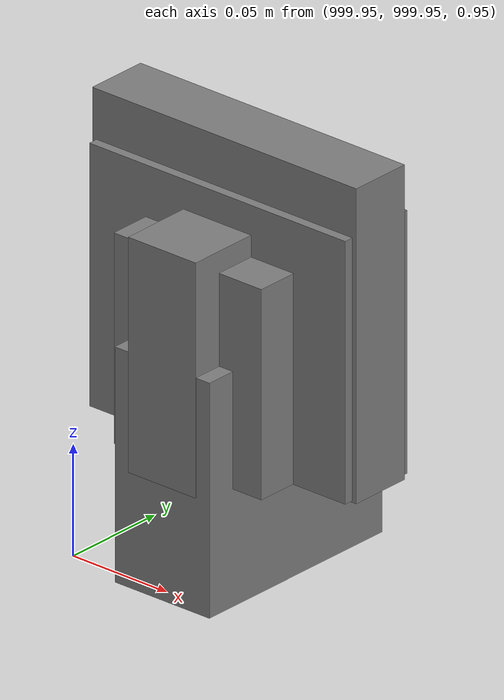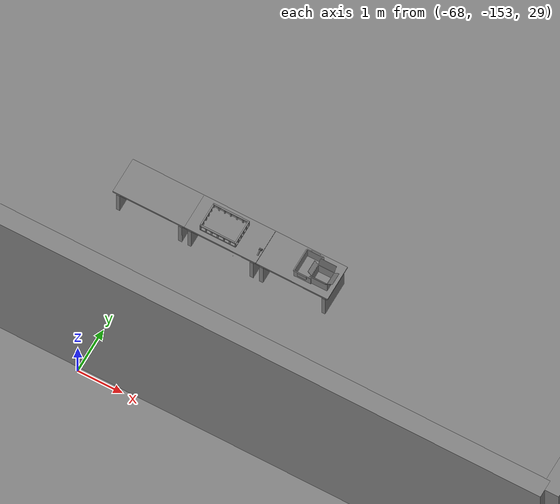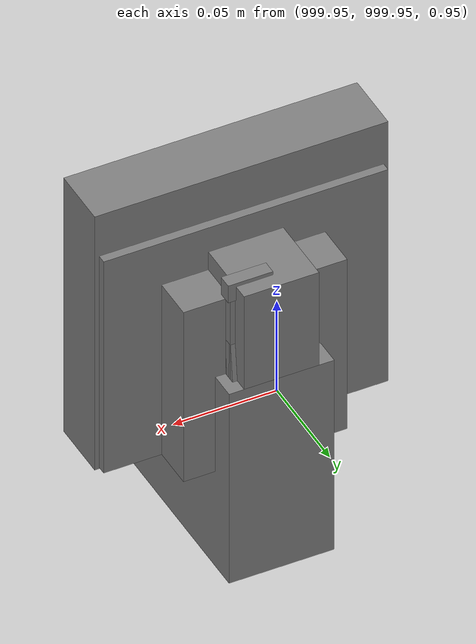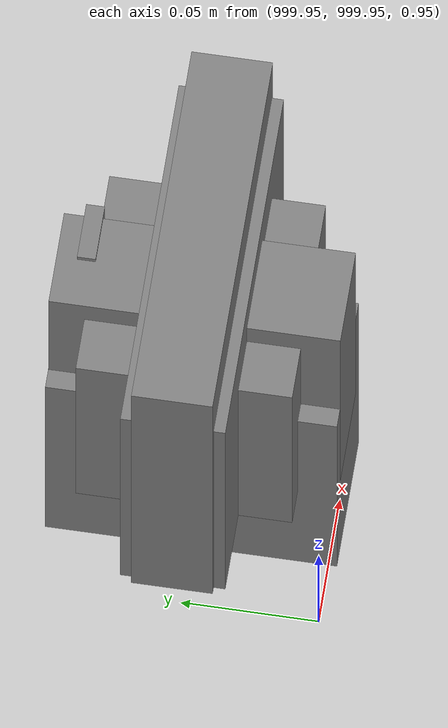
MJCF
<mujoco>
    <option gravity="0.000000000 0.000000000 -9.810000420" timestep="0.0049999999" integrator="implicitfast" density="1.225" viscosity="1.8000001e-05" noslip_iterations="10" iterations="100" sdf_iterations="50">
        <flag multiccd="disable"/>
    </option>
    <size memory="1000M"/>
    <compiler coordinate="local"/>
    <worldbody>
        <light cutoff="30" pos="0 1 1" dir="0 -1 -2"/>
        <light cutoff="30" pos="0 -1 1" dir="0 1 -2"/>
        <body pos="-64.866622925 -149.383972168 30.183746338" euler="89.999984741 89.999946594 0.000000000" name="openloong_gripper_2f85_fix_base_usda_bluebox_01">
            <geom contype="1" conaffinity="1" density="1000" type="box" material="" rgba="0.500000000 0.500000000 0.500000000 1.000000000" solimp="0.899999976 0.949999988 0.001000000" friction="1.000000000 0.005000000 0.000100000" solref="0.020000000 1.000000000" margin="0" condim="3" group="0" pos="0.276580811 0.187225342 0.000068665" quat="0.707106948 0.000077471 0.707106352 0.000077486" size="0.100000001 0.057999998 0.010000000" name="openloong_gripper_2f85_fix_base_usda_geom_2A672975_3788_495E_B403_C9636E9F6B72"/>
            <geom contype="1" conaffinity="1" density="1000" type="box" material="" rgba="0.500000000 0.500000000 0.500000000 1.000000000" solimp="0.899999976 0.949999988 0.001000000" friction="1.000000000 0.005000000 0.000100000" solref="0.020000000 1.000000000" margin="0" condim="3" group="0" pos="0.000000000 0.002883911 0.000000000" quat="0.999999881 0.000000000 0.000000000 0.000000000" size="0.254000008 0.003000000 0.172000006" name="openloong_gripper_2f85_fix_base_usda_geom_645E5BE7_32C5_4988_A4FB_D285E861523F"/>
            <geom contype="1" conaffinity="1" density="1000" type="box" material="" rgba="0.500000000 0.500000000 0.500000000 1.000000000" solimp="0.899999976 0.949999988 0.001000000" friction="1.000000000 0.005000000 0.000100000" solref="0.020000000 1.000000000" margin="0" condim="3" group="0" pos="0.000000000 0.124874115 0.173484802" quat="0.999796331 0.020176515 -0.000000015 0.000000030" size="0.259999990 0.119999997 0.007000000" name="openloong_gripper_2f85_fix_base_usda_geom_5FE3B649_942A_4612_AB37_716FE0ABD742"/>
            <geom contype="1" conaffinity="1" density="1000" type="box" material="" rgba="0.500000000 0.500000000 0.500000000 1.000000000" solimp="0.899999976 0.949999988 0.001000000" friction="1.000000000 0.005000000 0.000100000" solref="0.020000000 1.000000000" margin="0" condim="3" group="0" pos="0.000000000 0.124874115 -0.173469543" quat="0.999796331 -0.020176545 -0.000000015 0.000000000" size="0.259999990 0.119999997 0.007000000" name="openloong_gripper_2f85_fix_base_usda_geom_0ED99C8B_69C8_4E03_8535_D47B34F36D36"/>
            <geom contype="1" conaffinity="1" density="1000" type="box" material="" rgba="0.500000000 0.500000000 0.500000000 1.000000000" solimp="0.899999976 0.949999988 0.001000000" friction="1.000000000 0.005000000 0.000100000" solref="0.020000000 1.000000000" margin="0" condim="3" group="0" pos="0.000000000 0.214008331 0.188980103" quat="0.999912977 0.013176724 0.000000015 0.000000000" size="0.259999990 0.029999999 0.012500000" name="openloong_gripper_2f85_fix_base_usda_geom_D2ECC4EC_DDC3_4B91_BA32_E685C031683F"/>
            <geom contype="1" conaffinity="1" density="1000" type="box" material="" rgba="0.500000000 0.500000000 0.500000000 1.000000000" solimp="0.899999976 0.949999988 0.001000000" friction="1.000000000 0.005000000 0.000100000" solref="0.020000000 1.000000000" margin="0" condim="3" group="0" pos="-0.258361816 0.125289917 0.001876831" quat="0.702796936 -0.020792112 0.710783124 0.020769298" size="0.189999998 0.119999997 0.009000000" name="openloong_gripper_2f85_fix_base_usda_geom_7E38A25A_C9AA_4B89_A404_B0D2253FCA02"/>
            <geom contype="1" conaffinity="1" density="1000" type="box" material="" rgba="0.500000000 0.500000000 0.500000000 1.000000000" solimp="0.899999976 0.949999988 0.001000000" friction="1.000000000 0.005000000 0.000100000" solref="0.020000000 1.000000000" margin="0" condim="3" group="0" pos="0.000000000 0.214008331 -0.188980103" quat="0.999912977 -0.013176769 0.000000030 0.000000015" size="0.259999990 0.029999999 0.012500000" name="openloong_gripper_2f85_fix_base_usda_geom_F68710A5_683A_4ADD_A0DF_00C1F05E8144"/>
            <geom contype="1" conaffinity="1" density="1000" type="box" material="" rgba="0.500000000 0.500000000 0.500000000 1.000000000" solimp="0.899999976 0.949999988 0.001000000" friction="1.000000000 0.005000000 0.000100000" solref="0.020000000 1.000000000" margin="0" condim="3" group="0" pos="-0.276611328 0.187225342 0.000068665" quat="0.707106650 0.000077441 0.707106709 0.000077456" size="0.100000001 0.057999998 0.010000000" name="openloong_gripper_2f85_fix_base_usda_geom_3227E10E_52D1_4B9D_9EF2_226AC8BF7190"/>
            <geom contype="1" conaffinity="1" density="1000" type="box" material="" rgba="0.500000000 0.500000000 0.500000000 1.000000000" solimp="0.899999976 0.949999988 0.001000000" friction="1.000000000 0.005000000 0.000100000" solref="0.020000000 1.000000000" margin="0" condim="3" group="0" pos="0.258331299 0.125289917 0.001876831" quat="0.702851415 0.018856421 0.710823774 -0.019329369" size="0.189999998 0.119999997 0.009000000" name="openloong_gripper_2f85_fix_base_usda_geom_D7AC56CE_4F82_4199_B7DE_806902C19AE6"/>
            <freejoint name="openloong_gripper_2f85_fix_base_usda_bluebox_01_joint"/>
            <site size="0.005000000 0.005000000 0.005000000" rgba="0.500000000 0.500000000 0.500000000 1.000000000" pos="0.000000000 0.000000000 0.000000000" quat="0.999961913 0.008726534 0.000000000 0.000000000" group="0" type="sphere" name="openloong_gripper_2f85_fix_base_usda_bluebox_01site"/>
        </body>
        <body pos="-64.496299744 -149.491867065 30.235729218" euler="0.000000000 0.000000000 89.999946594" name="openloong_gripper_2f85_fix_base_usda_cardboardbox_01">
            <geom contype="1" conaffinity="1" density="1000" type="box" material="" rgba="0.500000000 0.500000000 0.500000000 1.000000000" solimp="0.899999976 0.949999988 0.001000000" friction="1.000000000 0.005000000 0.000100000" solref="0.020000000 1.000000000" margin="0" condim="3" group="0" pos="-0.003166199 -0.004086494 0.005052090" quat="1.000000000 0.000000000 0.000000000 0.000000000" size="0.142499998 0.177500010 0.005000000" name="openloong_gripper_2f85_fix_base_usda_geom_A7731678_3D75_4D35_8270_F38792455D77"/>
            <geom contype="1" conaffinity="1" density="1000" type="box" material="" rgba="0.500000000 0.500000000 0.500000000 1.000000000" solimp="0.899999976 0.949999988 0.001000000" friction="1.000000000 0.005000000 0.000100000" solref="0.020000000 1.000000000" margin="0" condim="3" group="0" pos="-0.003166199 0.170316696 0.150570869" quat="1.000000000 0.000000000 0.000000000 0.000000000" size="0.142499998 0.005000000 0.149999991" name="openloong_gripper_2f85_fix_base_usda_geom_AB989F44_0101_456D_8456_2D78B96CAE86"/>
            <geom contype="1" conaffinity="1" density="1000" type="box" material="" rgba="0.500000000 0.500000000 0.500000000 1.000000000" solimp="0.899999976 0.949999988 0.001000000" friction="1.000000000 0.005000000 0.000100000" solref="0.020000000 1.000000000" margin="0" condim="3" group="0" pos="-0.147399902 -0.005307198 0.150570869" quat="1.000000000 0.000000000 0.000000000 0.000000000" size="0.005000000 0.177500010 0.149999991" name="openloong_gripper_2f85_fix_base_usda_geom_6770FDC3_E8DF_46D6_A8DC_413323EFE2A1"/>
            <geom contype="1" conaffinity="1" density="1000" type="box" material="" rgba="0.500000000 0.500000000 0.500000000 1.000000000" solimp="0.899999976 0.949999988 0.001000000" friction="1.000000000 0.005000000 0.000100000" solref="0.020000000 1.000000000" margin="0" condim="3" group="0" pos="0.140275955 -0.005307198 0.150570869" quat="1.000000000 0.000000000 0.000000000 0.000000000" size="0.005000000 0.177500010 0.149999991" name="openloong_gripper_2f85_fix_base_usda_geom_243653CD_513C_4117_93A2_94B5944EC21E"/>
            <geom contype="1" conaffinity="1" density="1000" type="box" material="" rgba="0.500000000 0.500000000 0.500000000 1.000000000" solimp="0.899999976 0.949999988 0.001000000" friction="1.000000000 0.005000000 0.000100000" solref="0.020000000 1.000000000" margin="0" condim="3" group="0" pos="-0.003166199 -0.181550980 0.150570869" quat="1.000000000 0.000000000 0.000000000 0.000000000" size="0.142499998 0.005000000 0.149999991" name="openloong_gripper_2f85_fix_base_usda_geom_EDBC6C65_49D1_4604_8A21_E6E6FEC639EE"/>
            <freejoint name="openloong_gripper_2f85_fix_base_usda_cardboardbox_01_joint"/>
            <site size="0.005000000 0.005000000 0.005000000" rgba="0.500000000 0.500000000 0.500000000 1.000000000" pos="0.000000000 0.000000000 0.000000000" quat="0.999961913 0.008726535 0.000000000 0.000000000" group="0" type="sphere" name="openloong_gripper_2f85_fix_base_usda_site_D8A48E8B_6C47_48D9_BA76_CE93A91069FC"/>
            <body pos="0.139160156 -0.004048347 0.301930904" euler="-179.999954224 49.383502960 179.999954224" name="openloong_gripper_2f85_fix_base_usda_A1_006">
                <geom contype="1" conaffinity="1" density="1000" type="box" material="" rgba="0.500000000 0.500000000 0.500000000 1.000000000" solimp="0.899999976 0.949999988 0.001000000" friction="1.000000000 0.005000000 0.000100000" solref="0.020000000 1.000000000" margin="0" condim="3" group="0" pos="-0.071587563 0.000009537 0.001745224" quat="0.999999881 0.000000000 0.000000000 0.000000000" size="0.071249999 0.179999992 0.002500000" name="openloong_gripper_2f85_fix_base_usda_geom_9FFDD6FA_BEAF_4447_8F7F_73C004DF269B"/>
                <joint armature="0" stiffness="0.07" damping="0.0099999998" axis="0.000000 1.000000 0.000000" type="hinge" name="openloong_gripper_2f85_fix_base_usda_A1_006"/>
            </body>
            <body pos="-0.145902634 -0.004086494 0.301938057" euler="-180.000000000 -60.000011444 -180.000000000" name="openloong_gripper_2f85_fix_base_usda_A2_006">
                <geom contype="1" conaffinity="1" density="1000" type="box" material="" rgba="0.500000000 0.500000000 0.500000000 1.000000000" solimp="0.899999976 0.949999988 0.001000000" friction="1.000000000 0.005000000 0.000100000" solref="0.020000000 1.000000000" margin="0" condim="3" group="0" pos="0.071268082 0.000009537 0.002717972" quat="0.000002921 0.000000000 -0.000000030 0.999999881" size="0.071249999 0.179999992 0.002500000" name="openloong_gripper_2f85_fix_base_usda_geom_114931C6_6503_41AF_8770_7714C71CDE3D"/>
                <joint armature="0" stiffness="0.07" damping="0.0099999998" axis="0.000000 1.000000 0.000000" type="hinge" name="openloong_gripper_2f85_fix_base_usda_A2_006"/>
            </body>
            <body pos="-0.003385544 0.175991058 0.301930904" euler="-125.858116150 -0.000004561 0.000002331" name="openloong_gripper_2f85_fix_base_usda_B2_006">
                <geom contype="1" conaffinity="1" density="1000" type="box" material="" rgba="0.500000000 0.500000000 0.500000000 1.000000000" solimp="0.899999976 0.949999988 0.001000000" friction="1.000000000 0.005000000 0.000100000" solref="0.020000000 1.000000000" margin="0" condim="3" group="0" pos="0.000009537 -0.070939064 -0.002470016" quat="0.999614120 0.027776197 -0.000000015 0.000000030" size="0.137500003 0.064999998 0.005000000" name="openloong_gripper_2f85_fix_base_usda_geom_986915F6_6D22_48ED_9C5E_559E42B7C2F8"/>
                <joint armature="0" stiffness="0.07" damping="0.0099999998" axis="1.000000 0.000000 0.000000" type="hinge" name="openloong_gripper_2f85_fix_base_usda_B2_006"/>
            </body>
            <body pos="-0.003385544 -0.184140205 0.301938057" euler="147.805557251 0.000000000 0.000000000" name="openloong_gripper_2f85_fix_base_usda_B1_006">
                <geom contype="1" conaffinity="1" density="1000" type="box" material="" rgba="0.500000000 0.500000000 0.500000000 1.000000000" solimp="0.899999976 0.949999988 0.001000000" friction="1.000000000 0.005000000 0.000100000" solref="0.020000000 1.000000000" margin="0" condim="3" group="0" pos="-0.000028610 0.070202351 -0.002703667" quat="0.999614179 -0.027776167 0.000000000 0.000000000" size="0.137500003 0.064999998 0.005000000" name="openloong_gripper_2f85_fix_base_usda_geom_81C15A82_618F_4FE8_B642_68D0B543BDEF"/>
                <joint armature="0" stiffness="0.07" damping="0.0099999998" axis="1.000000 0.000000 0.000000" type="hinge" name="openloong_gripper_2f85_fix_base_usda_B1_006"/>
            </body>
        </body>
        <body pos="-65.882858276 -149.481979370 30.229999542" euler="-64.487716675 0.000000000 0.000000000" name="openloong_gripper_2f85_fix_base_usda_Barcode">
            <geom contype="1" conaffinity="1" density="1000" type="box" material="" rgba="0.500000000 0.500000000 0.500000000 1.000000000" solimp="0.899999976 0.949999988 0.001000000" friction="1.000000000 0.005000000 0.000100000" solref="0.020000000 1.000000000" margin="0" condim="3" group="0" pos="0.000000000 0.013038635 0.001419067" quat="0.000000000 0.000000000 0.000000000 1.000000119" size="0.034000002 0.010000000 0.017999999" name="openloong_gripper_2f85_fix_base_usda_geom_15F66327_BD3E_4942_B373_67E2873E4E38"/>
            <geom contype="1" conaffinity="1" density="1000" type="box" material="" rgba="0.500000000 0.500000000 0.500000000 1.000000000" solimp="0.899999976 0.949999988 0.001000000" friction="1.000000000 0.005000000 0.000100000" solref="0.020000000 1.000000000" margin="0" condim="3" group="0" pos="0.000000000 -0.035301208 -0.007095337" quat="0.000000000 0.000000000 -0.043619365 0.999048233" size="0.028999999 0.010000000 0.020000000" name="openloong_gripper_2f85_fix_base_usda_geom_4A589503_8A38_410C_A6EE_8399FA2D9ED5"/>
            <geom contype="1" conaffinity="1" density="1000" type="box" material="" rgba="0.500000000 0.500000000 0.500000000 1.000000000" solimp="0.899999976 0.949999988 0.001000000" friction="1.000000000 0.005000000 0.000100000" solref="0.020000000 1.000000000" margin="0" condim="3" group="0" pos="0.000000000 -0.043411255 -0.011749268" quat="0.922262907 0.386563420 0.000000000 0.000000000" size="0.026000001 0.010000000 0.020000000" name="openloong_gripper_2f85_fix_base_usda_geom_2873AFF2_A6C5_4E83_8E7D_15E5A38E57A8"/>
            <geom contype="1" conaffinity="1" density="1000" type="box" material="" rgba="0.500000000 0.500000000 0.500000000 1.000000000" solimp="0.899999976 0.949999988 0.001000000" friction="1.000000000 0.005000000 0.000100000" solref="0.020000000 1.000000000" margin="0" condim="3" group="0" pos="0.000000000 -0.016967773 -0.031860352" quat="0.000000000 0.000000000 0.000000000 1.000000119" size="0.008000000 0.010000000 0.013000000" name="openloong_gripper_2f85_fix_base_usda_geom_15C0E544_F4E4_4DE2_9927_0420D41A2EC9"/>
            <geom contype="1" conaffinity="1" density="1000" type="box" material="" rgba="0.500000000 0.500000000 0.500000000 1.000000000" solimp="0.899999976 0.949999988 0.001000000" friction="1.000000000 0.005000000 0.000100000" solref="0.020000000 1.000000000" margin="0" condim="3" group="0" pos="0.000000000 -0.001869202 0.000312805" quat="0.953716993 0.300705761 0.000000000 0.000000000" size="0.032000002 0.010000000 0.018999999" name="openloong_gripper_2f85_fix_base_usda_geom_E3AB5433_63C6_41BF_9D7A_FCB4A91B538D"/>
            <geom contype="1" conaffinity="1" density="1000" type="box" material="" rgba="0.500000000 0.500000000 0.500000000 1.000000000" solimp="0.899999976 0.949999988 0.001000000" friction="1.000000000 0.005000000 0.000100000" solref="0.020000000 1.000000000" margin="0" condim="3" group="0" pos="0.000000000 -0.019531250 -0.003173828" quat="0.953716993 0.300705761 0.000000000 0.000000000" size="0.030999999 0.010000000 0.020000000" name="openloong_gripper_2f85_fix_base_usda_geom_5343B3B8_A6CE_4263_8045_69FDDD87A444"/>
            <geom contype="1" conaffinity="1" density="1000" type="box" material="" rgba="0.500000000 0.500000000 0.500000000 1.000000000" solimp="0.899999976 0.949999988 0.001000000" friction="1.000000000 0.005000000 0.000100000" solref="0.020000000 1.000000000" margin="0" condim="3" group="0" pos="0.000000000 -0.035301208 -0.007095337" quat="0.953716993 0.300705761 0.000000000 0.000000000" size="0.028999999 0.010000000 0.020000000" name="openloong_gripper_2f85_fix_base_usda_geom_A930FC2E_F429_491C_B99F_1C0F9D53ECA1"/>
            <geom contype="1" conaffinity="1" density="1000" type="box" material="" rgba="0.500000000 0.500000000 0.500000000 1.000000000" solimp="0.899999976 0.949999988 0.001000000" friction="1.000000000 0.005000000 0.000100000" solref="0.020000000 1.000000000" margin="0" condim="3" group="0" pos="0.000000000 -0.042617798 -0.071121216" quat="0.000000000 0.000000000 0.000000000 1.000000119" size="0.013000000 0.021000000 0.059999999" name="openloong_gripper_2f85_fix_base_usda_geom_4E077287_EF2C_462D_A476_3071D579DA46"/>
            <freejoint name="openloong_gripper_2f85_fix_base_usda_Barcode_joint"/>
            <site size="0.005000000 0.005000000 0.005000000" rgba="0.500000000 0.500000000 0.500000000 1.000000000" pos="0.000000000 0.000000000 0.000000000" quat="1.000000000 0.000000000 0.000000000 0.000000000" group="0" type="sphere" name="openloong_gripper_2f85_fix_base_usda_Barcode_site"/>
        </body>
        <body pos="-66.745018005 -149.392349243 30.184000015" euler="0.000000000 0.000000000 89.999946594" name="[22330483927619]_Basket_01">
            <geom contype="1" conaffinity="1" density="1000" type="box" material="" rgba="0.500000000 0.500000000 0.500000000 1.000000000" solimp="0.899999976 0.949999988 0.001000000" friction="1.000000000 0.005000000 0.000100000" solref="0.020000000 1.000000000" margin="0" condim="3" group="0" pos="-0.052425385 0.389207840 0.089787483" quat="0.707107008 0.000000000 0.000000000 0.707106411" size="0.014249999 0.014249999 0.059999999" name="[22330483927619]_geom_C5B5DEF7_E438_497E_ADAD_7353F162C51B"/>
            <geom contype="1" conaffinity="1" density="1000" type="box" material="" rgba="0.500000000 0.500000000 0.500000000 1.000000000" solimp="0.899999976 0.949999988 0.001000000" friction="1.000000000 0.005000000 0.000100000" solref="0.020000000 1.000000000" margin="0" condim="3" group="0" pos="0.264015198 -0.133043289 0.089787483" quat="0.707107008 0.000000000 0.000000000 0.707106411" size="0.014249999 0.014249999 0.059999999" name="[22330483927619]_geom_D6F09E7D_5E12_4ABA_B9C3_FC6CA8366B1A"/>
            <geom contype="1" conaffinity="1" density="1000" type="box" material="" rgba="0.500000000 0.500000000 0.500000000 1.000000000" solimp="0.899999976 0.949999988 0.001000000" friction="1.000000000 0.005000000 0.000100000" solref="0.020000000 1.000000000" margin="0" condim="3" group="0" pos="-0.264015198 -0.265548706 0.089793205" quat="0.707107008 0.000000000 0.000000000 0.707106411" size="0.014249999 0.014249999 0.059999999" name="[22330483927619]_geom_C2FA48CA_9358_4DB9_B746_43D4AD0BAC26"/>
            <geom contype="1" conaffinity="1" density="1000" type="box" material="" rgba="0.500000000 0.500000000 0.500000000 1.000000000" solimp="0.899999976 0.949999988 0.001000000" friction="1.000000000 0.005000000 0.000100000" solref="0.020000000 1.000000000" margin="0" condim="3" group="0" pos="-0.160263062 -0.389322281 0.089793205" quat="0.707107008 0.000000000 0.000000000 0.707106411" size="0.014249999 0.014249999 0.059999999" name="[22330483927619]_geom_3C2DD6F3_C2E5_4E4B_8F13_24ED54A244BA"/>
            <geom contype="1" conaffinity="1" density="1000" type="box" material="" rgba="0.500000000 0.500000000 0.500000000 1.000000000" solimp="0.899999976 0.949999988 0.001000000" friction="1.000000000 0.005000000 0.000100000" solref="0.020000000 1.000000000" margin="0" condim="3" group="0" pos="0.162265778 -0.389322281 0.089787483" quat="0.707107008 0.000000000 0.000000000 0.707106411" size="0.014249999 0.014249999 0.059999999" name="[22330483927619]_geom_7D4179A3_46AE_4ECD_8CC8_5C50A3204753"/>
            <geom contype="1" conaffinity="1" density="1000" type="box" material="" rgba="0.500000000 0.500000000 0.500000000 1.000000000" solimp="0.899999976 0.949999988 0.001000000" friction="1.000000000 0.005000000 0.000100000" solref="0.020000000 1.000000000" margin="0" condim="3" group="0" pos="0.264015198 0.389207840 0.089787483" quat="0.707107008 0.000000000 0.000000000 0.707106411" size="0.014249999 0.014249999 0.059999999" name="[22330483927619]_geom_F7895155_75D7_46E8_9A0F_F6B7E9279CDD"/>
            <geom contype="1" conaffinity="1" density="1000" type="box" material="" rgba="0.500000000 0.500000000 0.500000000 1.000000000" solimp="0.899999976 0.949999988 0.001000000" friction="1.000000000 0.005000000 0.000100000" solref="0.020000000 1.000000000" margin="0" condim="3" group="0" pos="-0.264015198 -0.133043289 0.089793205" quat="0.707107008 0.000000000 0.000000000 0.707106411" size="0.014249999 0.014249999 0.059999999" name="[22330483927619]_geom_3442B7FA_91BB_4985_A0CD_42A48EBBC451"/>
            <geom contype="1" conaffinity="1" density="1000" type="box" material="" rgba="0.500000000 0.500000000 0.500000000 1.000000000" solimp="0.899999976 0.949999988 0.001000000" friction="1.000000000 0.005000000 0.000100000" solref="0.020000000 1.000000000" margin="0" condim="3" group="0" pos="-0.264026642 0.269256592 0.089793205" quat="0.707107008 0.000000000 0.000000000 0.707106411" size="0.014249999 0.014249999 0.059999999" name="[22330483927619]_geom_11D7F7D2_37BE_4DA0_BA0E_27D555397D97"/>
            <geom contype="1" conaffinity="1" density="1000" type="box" material="" rgba="0.500000000 0.500000000 0.500000000 1.000000000" solimp="0.899999976 0.949999988 0.001000000" friction="1.000000000 0.005000000 0.000100000" solref="0.020000000 1.000000000" margin="0" condim="3" group="0" pos="0.054462433 0.389207840 0.089787483" quat="0.707107008 0.000000000 0.000000000 0.707106411" size="0.014249999 0.014249999 0.059999999" name="[22330483927619]_geom_59597FB3_287F_48FA_A2BF_BA27E7A00BF9"/>
            <geom contype="1" conaffinity="1" density="1000" type="box" material="" rgba="0.500000000 0.500000000 0.500000000 1.000000000" solimp="0.899999976 0.949999988 0.001000000" friction="1.000000000 0.005000000 0.000100000" solref="0.020000000 1.000000000" margin="0" condim="3" group="0" pos="0.054462433 -0.389322281 0.089787483" quat="0.707107008 0.000000000 0.000000000 0.707106411" size="0.014249999 0.014249999 0.059999999" name="[22330483927619]_geom_685F3758_AC56_4A5D_BD63_7F007DF62A36"/>
            <geom contype="1" conaffinity="1" density="1000" type="box" material="" rgba="0.500000000 0.500000000 0.500000000 1.000000000" solimp="0.899999976 0.949999988 0.001000000" friction="1.000000000 0.005000000 0.000100000" solref="0.020000000 1.000000000" margin="0" condim="3" group="0" pos="0.264015198 0.269256592 0.089793205" quat="0.707107008 0.000000000 0.000000000 0.707106411" size="0.014249999 0.014249999 0.059999999" name="[22330483927619]_geom_C1364214_0D46_4E12_8E66_1795D23E091E"/>
            <geom contype="1" conaffinity="1" density="1000" type="box" material="" rgba="0.500000000 0.500000000 0.500000000 1.000000000" solimp="0.899999976 0.949999988 0.001000000" friction="1.000000000 0.005000000 0.000100000" solref="0.020000000 1.000000000" margin="0" condim="3" group="0" pos="0.264015198 -0.389322281 0.089787483" quat="0.707107008 0.000000000 0.000000000 0.707106411" size="0.014249999 0.014249999 0.059999999" name="[22330483927619]_geom_8B21FED2_E9CB_4FBF_902A_738438E28F4C"/>
            <geom contype="1" conaffinity="1" density="1000" type="box" material="" rgba="0.500000000 0.500000000 0.500000000 1.000000000" solimp="0.899999976 0.949999988 0.001000000" friction="1.000000000 0.005000000 0.000100000" solref="0.020000000 1.000000000" margin="0" condim="3" group="0" pos="0.000000000 0.000000000 0.015998840" quat="0.707107008 0.000000000 0.000000000 0.707106411" size="0.403499991 0.279000014 0.015750000" name="[22330483927619]_geom_CEED7EB3_E044_4EA2_BA65_F52682267EE5"/>
            <geom contype="1" conaffinity="1" density="1000" type="box" material="" rgba="0.500000000 0.500000000 0.500000000 1.000000000" solimp="0.899999976 0.949999988 0.001000000" friction="1.000000000 0.005000000 0.000100000" solref="0.020000000 1.000000000" margin="0" condim="3" group="0" pos="0.000000000 -0.389476776 0.163619041" quat="0.707107008 0.000000000 0.000000000 0.707106411" size="0.015000000 0.277500004 0.015750000" name="[22330483927619]_geom_C093A01B_4945_4A3F_8A4E_EE0CB603EB19"/>
            <geom contype="1" conaffinity="1" density="1000" type="box" material="" rgba="0.500000000 0.500000000 0.500000000 1.000000000" solimp="0.899999976 0.949999988 0.001000000" friction="1.000000000 0.005000000 0.000100000" solref="0.020000000 1.000000000" margin="0" condim="3" group="0" pos="0.162265778 0.389207840 0.089787483" quat="0.707107008 0.000000000 0.000000000 0.707106411" size="0.014249999 0.014249999 0.059999999" name="[22330483927619]_geom_9DEADA78_3EAE_469E_A808_7AFFFC43E588"/>
            <geom contype="1" conaffinity="1" density="1000" type="box" material="" rgba="0.500000000 0.500000000 0.500000000 1.000000000" solimp="0.899999976 0.949999988 0.001000000" friction="1.000000000 0.005000000 0.000100000" solref="0.020000000 1.000000000" margin="0" condim="3" group="0" pos="0.000000000 0.389471054 0.163619041" quat="0.707107008 0.000000000 0.000000000 0.707106411" size="0.015000000 0.277500004 0.015750000" name="[22330483927619]_geom_F8B8E7B5_78AC_46FC_A9FA_967B21B9B56A"/>
            <geom contype="1" conaffinity="1" density="1000" type="box" material="" rgba="0.500000000 0.500000000 0.500000000 1.000000000" solimp="0.899999976 0.949999988 0.001000000" friction="1.000000000 0.005000000 0.000100000" solref="0.020000000 1.000000000" margin="0" condim="3" group="0" pos="-0.263511658 0.000000000 0.163619041" quat="0.707107008 0.000000000 0.000000000 0.707106411" size="0.403499991 0.015000000 0.015750000" name="[22330483927619]_geom_191FDC96_C742_4DEA_B9EF_D31EAC91D363"/>
            <geom contype="1" conaffinity="1" density="1000" type="box" material="" rgba="0.500000000 0.500000000 0.500000000 1.000000000" solimp="0.899999976 0.949999988 0.001000000" friction="1.000000000 0.005000000 0.000100000" solref="0.020000000 1.000000000" margin="0" condim="3" group="0" pos="-0.264015198 0.141334534 0.089793205" quat="0.707107008 0.000000000 0.000000000 0.707106411" size="0.014249999 0.014249999 0.059999999" name="[22330483927619]_geom_FC9EB80D_8A23_4F2F_B261_CA94F483D395"/>
            <geom contype="1" conaffinity="1" density="1000" type="box" material="" rgba="0.500000000 0.500000000 0.500000000 1.000000000" solimp="0.899999976 0.949999988 0.001000000" friction="1.000000000 0.005000000 0.000100000" solref="0.020000000 1.000000000" margin="0" condim="3" group="0" pos="0.264015198 -0.265548706 0.089787483" quat="0.707107008 0.000000000 0.000000000 0.707106411" size="0.014249999 0.014249999 0.059999999" name="[22330483927619]_geom_3B30659F_0D8C_430D_904F_D4350B2FA94E"/>
            <geom contype="1" conaffinity="1" density="1000" type="box" material="" rgba="0.500000000 0.500000000 0.500000000 1.000000000" solimp="0.899999976 0.949999988 0.001000000" friction="1.000000000 0.005000000 0.000100000" solref="0.020000000 1.000000000" margin="0" condim="3" group="0" pos="-0.160263062 0.389207840 0.089787483" quat="0.707107008 0.000000000 0.000000000 0.707106411" size="0.014249999 0.014249999 0.059999999" name="[22330483927619]_geom_22D0FCD9_0434_4586_AEDB_0245434DE99B"/>
            <geom contype="1" conaffinity="1" density="1000" type="box" material="" rgba="0.500000000 0.500000000 0.500000000 1.000000000" solimp="0.899999976 0.949999988 0.001000000" friction="1.000000000 0.005000000 0.000100000" solref="0.020000000 1.000000000" margin="0" condim="3" group="0" pos="-0.052425385 -0.389322281 0.089787483" quat="0.707107008 0.000000000 0.000000000 0.707106411" size="0.014249999 0.014249999 0.059999999" name="[22330483927619]_geom_BE24BEC9_EE6D_4F0F_B553_4FCCF9A7FF22"/>
            <geom contype="1" conaffinity="1" density="1000" type="box" material="" rgba="0.500000000 0.500000000 0.500000000 1.000000000" solimp="0.899999976 0.949999988 0.001000000" friction="1.000000000 0.005000000 0.000100000" solref="0.020000000 1.000000000" margin="0" condim="3" group="0" pos="-0.264026642 -0.389322281 0.089793205" quat="0.707107008 0.000000000 0.000000000 0.707106411" size="0.014249999 0.014249999 0.059999999" name="[22330483927619]_geom_21088545_41EC_4691_B461_C551A611D227"/>
            <geom contype="1" conaffinity="1" density="1000" type="box" material="" rgba="0.500000000 0.500000000 0.500000000 1.000000000" solimp="0.899999976 0.949999988 0.001000000" friction="1.000000000 0.005000000 0.000100000" solref="0.020000000 1.000000000" margin="0" condim="3" group="0" pos="0.264015198 0.141334534 0.089787483" quat="0.707107008 0.000000000 0.000000000 0.707106411" size="0.014249999 0.014249999 0.059999999" name="[22330483927619]_geom_E8D10C2F_906A_492C_B868_807A4A767492"/>
            <geom contype="1" conaffinity="1" density="1000" type="box" material="" rgba="0.500000000 0.500000000 0.500000000 1.000000000" solimp="0.899999976 0.949999988 0.001000000" friction="1.000000000 0.005000000 0.000100000" solref="0.020000000 1.000000000" margin="0" condim="3" group="0" pos="-0.264015198 0.389207840 0.089793205" quat="0.707107008 0.000000000 0.000000000 0.707106411" size="0.014249999 0.014249999 0.059999999" name="[22330483927619]_geom_A2B05A93_A168_424B_96BE_AC387722F1A8"/>
            <geom contype="1" conaffinity="1" density="1000" type="box" material="" rgba="0.500000000 0.500000000 0.500000000 1.000000000" solimp="0.899999976 0.949999988 0.001000000" friction="1.000000000 0.005000000 0.000100000" solref="0.020000000 1.000000000" margin="0" condim="3" group="0" pos="0.264015198 0.004480362 0.089787483" quat="0.707107008 0.000000000 0.000000000 0.707106411" size="0.014249999 0.014249999 0.059999999" name="[22330483927619]_geom_4B13DDBA_784D_4CFD_BF07_83E2C3871B68"/>
            <geom contype="1" conaffinity="1" density="1000" type="box" material="" rgba="0.500000000 0.500000000 0.500000000 1.000000000" solimp="0.899999976 0.949999988 0.001000000" friction="1.000000000 0.005000000 0.000100000" solref="0.020000000 1.000000000" margin="0" condim="3" group="0" pos="0.263694763 -0.000011444 0.163619041" quat="0.707107008 0.000000000 0.000000000 0.707106411" size="0.403499991 0.015000000 0.015750000" name="[22330483927619]_geom_6B1F3454_785B_447D_93BC_6DB0501F110A"/>
            <geom contype="1" conaffinity="1" density="1000" type="box" material="" rgba="0.500000000 0.500000000 0.500000000 1.000000000" solimp="0.899999976 0.949999988 0.001000000" friction="1.000000000 0.005000000 0.000100000" solref="0.020000000 1.000000000" margin="0" condim="3" group="0" pos="-0.264015198 0.004480362 0.089793205" quat="0.707107008 0.000000000 0.000000000 0.707106411" size="0.014249999 0.014249999 0.059999999" name="[22330483927619]_geom_A344CC84_87F0_4801_8D7C_4BC240929773"/>
            <freejoint name="[22330483927619]_joint_B2EB87CA_07EF_4879_91D5_DC6843241086"/>
        </body>
        <body pos="0.000000000 0.000000000 0.000000000" euler="0.000000000 0.000000000 0.000000000" name="Static Objects_Static Objects">
            <geom contype="1" conaffinity="1" density="1000" type="box" material="" rgba="0.500000000 0.500000000 0.500000000 1.000000000" solimp="0.899999976 0.949999988 0.001000000" friction="1.000000000 0.005000000 0.000100000" solref="0.020000000 1.000000000" margin="0" condim="3" group="0" pos="-67.544113159 -149.365814209 29.727830887" quat="0.500000417 0.499999970 0.499999553 0.499999970" size="0.381000012 0.319999993 0.041000001" name="Static Objects_geom_1F175E75_08E5_425F_BBE9_04EBC9763408"/>
            <geom contype="1" conaffinity="1" density="1000" type="box" material="" rgba="0.500000000 0.500000000 0.500000000 1.000000000" solimp="0.899999976 0.949999988 0.001000000" friction="1.000000000 0.005000000 0.000100000" solref="0.020000000 1.000000000" margin="0" condim="3" group="0" pos="-68.239501953 -149.365814209 30.086868286" quat="0.500000417 0.499999970 0.499999553 0.499999970" size="0.370999992 0.039500002 0.745000005" name="Static Objects_geom_0F8EA571_E98F_49A9_8274_D012F84371C1"/>
            <geom contype="1" conaffinity="1" density="1000" type="box" material="" rgba="0.500000000 0.500000000 0.500000000 1.000000000" solimp="0.899999976 0.949999988 0.001000000" friction="1.000000000 0.005000000 0.000100000" solref="0.020000000 1.000000000" margin="0" condim="3" group="0" pos="-68.239501953 -149.365814209 30.147235870" quat="0.500000417 0.499999970 0.499999553 0.499999970" size="0.400000006 0.022000000 0.800000012" name="Static Objects_geom_C3CDAFD2_B1A3_4420_A94C_DF86DC15B3E1"/>
            <geom contype="1" conaffinity="1" density="1000" type="box" material="" rgba="0.500000000 0.500000000 0.500000000 1.000000000" solimp="0.899999976 0.949999988 0.001000000" friction="1.000000000 0.005000000 0.000100000" solref="0.020000000 1.000000000" margin="0" condim="3" group="0" pos="-68.934890747 -149.365814209 29.727830887" quat="0.500000417 0.499999970 0.499999553 0.499999970" size="0.381000012 0.319999993 0.041000001" name="Static Objects_geom_00BBB1BA_5295_4884_9463_40549ADCC899"/>
            <geom contype="1" conaffinity="1" density="1000" type="box" material="" rgba="0.500000000 0.500000000 0.500000000 1.000000000" solimp="0.899999976 0.949999988 0.001000000" friction="1.000000000 0.005000000 0.000100000" solref="0.020000000 1.000000000" margin="0" condim="3" group="0" pos="-68.239501953 -149.365814209 29.561563492" quat="0.500000417 0.499999970 0.499999553 0.499999970" size="0.020000000 0.022000000 0.660000026" name="Static Objects_geom_46A29ECC_2553_4406_9A88_2956DEBFD1F5"/>
            <geom contype="1" conaffinity="1" density="1000" type="box" material="" rgba="0.500000000 0.500000000 0.500000000 1.000000000" solimp="0.899999976 0.949999988 0.001000000" friction="1.000000000 0.005000000 0.000100000" solref="0.020000000 1.000000000" margin="0" condim="3" group="0" pos="-65.945671082 -149.365814209 29.727830887" quat="0.500000417 0.499999970 0.499999553 0.499999970" size="0.381000012 0.319999993 0.041000001" name="Static Objects_geom_929A7242_F5AD_46D3_939E_EC8BC202701D"/>
            <geom contype="1" conaffinity="1" density="1000" type="box" material="" rgba="0.500000000 0.500000000 0.500000000 1.000000000" solimp="0.899999976 0.949999988 0.001000000" friction="1.000000000 0.005000000 0.000100000" solref="0.020000000 1.000000000" margin="0" condim="3" group="0" pos="-66.641059875 -149.365814209 30.086868286" quat="0.500000417 0.499999970 0.499999553 0.499999970" size="0.370999992 0.039500002 0.745000005" name="Static Objects_geom_580F5F37_F3A0_4273_A064_BD091C730EE0"/>
            <geom contype="1" conaffinity="1" density="1000" type="box" material="" rgba="0.500000000 0.500000000 0.500000000 1.000000000" solimp="0.899999976 0.949999988 0.001000000" friction="1.000000000 0.005000000 0.000100000" solref="0.020000000 1.000000000" margin="0" condim="3" group="0" pos="-66.641059875 -149.365814209 30.147235870" quat="0.500000417 0.499999970 0.499999553 0.499999970" size="0.400000006 0.022000000 0.800000012" name="Static Objects_geom_8B7D4254_64A6_41E7_A33F_5B754B09B89E"/>
            <geom contype="1" conaffinity="1" density="1000" type="box" material="" rgba="0.500000000 0.500000000 0.500000000 1.000000000" solimp="0.899999976 0.949999988 0.001000000" friction="1.000000000 0.005000000 0.000100000" solref="0.020000000 1.000000000" margin="0" condim="3" group="0" pos="-67.336448669 -149.365814209 29.727830887" quat="0.500000417 0.499999970 0.499999553 0.499999970" size="0.381000012 0.319999993 0.041000001" name="Static Objects_geom_DD5DC84C_BFF7_4467_BC71_7CD0A0F8A572"/>
            <geom contype="1" conaffinity="1" density="1000" type="box" material="" rgba="0.500000000 0.500000000 0.500000000 1.000000000" solimp="0.899999976 0.949999988 0.001000000" friction="1.000000000 0.005000000 0.000100000" solref="0.020000000 1.000000000" margin="0" condim="3" group="0" pos="-66.641059875 -149.365814209 29.561563492" quat="0.500000417 0.499999970 0.499999553 0.499999970" size="0.020000000 0.022000000 0.660000026" name="Static Objects_geom_5FD73731_C977_42C9_A68B_50E7FC8D6E81"/>
            <geom contype="1" conaffinity="1" density="1000" type="box" material="" rgba="0.500000000 0.500000000 0.500000000 1.000000000" solimp="0.899999976 0.949999988 0.001000000" friction="1.000000000 0.005000000 0.000100000" solref="0.020000000 1.000000000" margin="0" condim="3" group="0" pos="-64.338577271 -149.365814209 29.727830887" quat="0.500000417 0.499999970 0.499999553 0.499999970" size="0.381000012 0.319999993 0.041000001" name="Static Objects_geom_70B97549_7B11_483A_AD8B_0EE4F6DAEEB4"/>
            <geom contype="1" conaffinity="1" density="1000" type="box" material="" rgba="0.500000000 0.500000000 0.500000000 1.000000000" solimp="0.899999976 0.949999988 0.001000000" friction="1.000000000 0.005000000 0.000100000" solref="0.020000000 1.000000000" margin="0" condim="3" group="0" pos="-65.033966064 -149.365814209 30.086868286" quat="0.500000417 0.499999970 0.499999553 0.499999970" size="0.370999992 0.039500002 0.745000005" name="Static Objects_geom_1BF08D61_4C06_48BB_86BD_85B9A3F4D7EA"/>
            <geom contype="1" conaffinity="1" density="1000" type="box" material="" rgba="0.500000000 0.500000000 0.500000000 1.000000000" solimp="0.899999976 0.949999988 0.001000000" friction="1.000000000 0.005000000 0.000100000" solref="0.020000000 1.000000000" margin="0" condim="3" group="0" pos="-65.033966064 -149.365814209 30.147235870" quat="0.500000417 0.499999970 0.499999553 0.499999970" size="0.400000006 0.022000000 0.800000012" name="Static Objects_geom_CACB3A4C_3FAF_4546_91BA_24D07706F643"/>
            <geom contype="1" conaffinity="1" density="1000" type="box" material="" rgba="0.500000000 0.500000000 0.500000000 1.000000000" solimp="0.899999976 0.949999988 0.001000000" friction="1.000000000 0.005000000 0.000100000" solref="0.020000000 1.000000000" margin="0" condim="3" group="0" pos="-65.729354858 -149.365814209 29.727830887" quat="0.500000417 0.499999970 0.499999553 0.499999970" size="0.381000012 0.319999993 0.041000001" name="Static Objects_geom_9D2640A3_8CEF_4466_9236_6BC7BB954524"/>
            <geom contype="1" conaffinity="1" density="1000" type="box" material="" rgba="0.500000000 0.500000000 0.500000000 1.000000000" solimp="0.899999976 0.949999988 0.001000000" friction="1.000000000 0.005000000 0.000100000" solref="0.020000000 1.000000000" margin="0" condim="3" group="0" pos="-65.033966064 -149.365814209 29.561563492" quat="0.500000417 0.499999970 0.499999553 0.499999970" size="0.020000000 0.022000000 0.660000026" name="Static Objects_geom_F58C5FEB_F067_4065_B331_B35EBFFC5E12"/>
            <geom contype="1" conaffinity="1" density="1000" type="box" material="" rgba="0.500000000 0.500000000 0.500000000 1.000000000" solimp="0.899999976 0.949999988 0.001000000" friction="1.000000000 0.005000000 0.000100000" solref="0.020000000 1.000000000" margin="0" condim="3" group="0" pos="-61.754566193 -137.853729248 33.906845093" quat="0.707107067 0.000000000 0.000000000 0.707106471" size="0.759999990 0.759999990 4.500000000" name="Static Objects_geom_6F1503F0_AB0D_403B_BE7F_7FE92497D42A"/>
            <geom contype="1" conaffinity="1" density="1000" type="box" material="" rgba="0.500000000 0.500000000 0.500000000 1.000000000" solimp="0.899999976 0.949999988 0.001000000" friction="1.000000000 0.005000000 0.000100000" solref="0.020000000 1.000000000" margin="0" condim="3" group="0" pos="-57.511135101 -144.927108765 31.707921982" quat="1.000000000 0.000000000 0.000000000 0.000000000" size="0.200000003 8.000000000 2.299999952" name="Static Objects_geom_45901C70_12FB_4D25_86F8_258905B4CB44"/>
            <geom contype="1" conaffinity="1" density="1000" type="box" material="" rgba="0.500000000 0.500000000 0.500000000 1.000000000" solimp="0.899999976 0.949999988 0.001000000" friction="1.000000000 0.005000000 0.000100000" solref="0.020000000 1.000000000" margin="0" condim="3" group="0" pos="-80.517646790 -157.574050903 31.688196182" quat="0.707107067 0.000000000 0.000000000 0.707106471" size="0.600000024 0.600000024 2.299999952" name="Static Objects_geom_BC0ABC3E_9466_4EA0_9618_BD29B5485C97"/>
            <geom contype="1" conaffinity="1" density="1000" type="box" material="" rgba="0.500000000 0.500000000 0.500000000 1.000000000" solimp="0.899999976 0.949999988 0.001000000" friction="1.000000000 0.005000000 0.000100000" solref="0.020000000 1.000000000" margin="0" condim="3" group="0" pos="-80.711044312 -147.414932251 31.666158676" quat="1.000000000 0.000000000 0.000000000 0.000000000" size="0.200000003 10.000000000 2.299999952" name="Static Objects_geom_EAB3466B_15DC_4EC1_93D0_B47E345BA027"/>
            <geom contype="1" conaffinity="1" density="1000" type="box" material="" rgba="0.500000000 0.500000000 0.500000000 1.000000000" solimp="0.899999976 0.949999988 0.001000000" friction="1.000000000 0.005000000 0.000100000" solref="0.020000000 1.000000000" margin="0" condim="3" group="0" pos="-57.687217712 -137.434692383 31.688196182" quat="0.707107067 0.000000000 0.000000000 0.707106471" size="0.600000024 0.600000024 2.299999952" name="Static Objects_geom_871E4C51_3010_44FF_AA5B_C3901C41D995"/>
            <geom contype="1" conaffinity="1" density="1000" type="box" material="" rgba="0.500000000 0.500000000 0.500000000 1.000000000" solimp="0.899999976 0.949999988 0.001000000" friction="1.000000000 0.005000000 0.000100000" solref="0.020000000 1.000000000" margin="0" condim="3" group="0" pos="-69.537033081 -140.263229370 31.714921951" quat="0.707107067 0.000000000 0.000000000 0.707106471" size="0.759999990 4.500000000 2.299999952" name="Static Objects_geom_BEEBA69F_C5E7_4740_BD66_BABC3EFB2963"/>
            <geom contype="1" conaffinity="1" density="1000" type="box" material="" rgba="0.500000000 0.500000000 0.500000000 1.000000000" solimp="0.899999976 0.949999988 0.001000000" friction="1.000000000 0.005000000 0.000100000" solref="0.020000000 1.000000000" margin="0" condim="3" group="0" pos="-80.073638916 -137.853713989 33.906845093" quat="0.707107067 0.000000000 0.000000000 0.707106471" size="0.759999990 0.759999990 4.500000000" name="Static Objects_geom_DBB7736C_C445_4368_BA43_4344EACF8B25"/>
            <geom contype="1" conaffinity="1" density="1000" type="box" material="" rgba="0.500000000 0.500000000 0.500000000 1.000000000" solimp="0.899999976 0.949999988 0.001000000" friction="1.000000000 0.005000000 0.000100000" solref="0.020000000 1.000000000" margin="0" condim="3" group="0" pos="-73.406707764 -155.734664917 31.707921982" quat="1.000000000 0.000000000 0.000000000 0.000000000" size="0.200000003 3.000000000 2.299999952" name="Static Objects_geom_BA95FB4E_345F_46B6_A9D0_AF5D891A9524"/>
            <geom contype="1" conaffinity="1" density="1000" type="box" material="" rgba="0.500000000 0.500000000 0.500000000 1.000000000" solimp="0.899999976 0.949999988 0.001000000" friction="1.000000000 0.005000000 0.000100000" solref="0.020000000 1.000000000" margin="0" condim="3" group="0" pos="-68.497543335 -137.448257446 31.707921982" quat="0.707107067 0.000000000 0.000000000 0.707106471" size="0.200000003 14.000000000 2.299999952" name="Static Objects_geom_CB84AF1A_F89A_47A8_9AE9_AF9E6C6F153A"/>
            <geom contype="1" conaffinity="1" density="1000" type="cylinder" material="" rgba="0.500000000 0.500000000 0.500000000 1.000000000" solimp="0.899999976 0.949999988 0.001000000" friction="1.000000000 0.005000000 0.000100000" solref="0.020000000 1.000000000" margin="0" condim="3" group="0" pos="-68.868522644 -142.134506226 31.711090088" quat="0.707107067 0.000000000 0.000000000 0.707106471" size="0.509999990 2.299999952 1.000000000" name="Static Objects_geom_62D8ADF3_7A91_4A5D_8EB4_50D7AA3D9F4C"/>
            <geom contype="1" conaffinity="1" density="1000" type="plane" material="" rgba="0.500000000 0.500000000 0.500000000 1.000000000" solimp="0.899999976 0.949999988 0.001000000" friction="1.000000000 0.005000000 0.000100000" solref="0.020000000 1.000000000" margin="0" condim="3" group="0" pos="-72.873703003 -147.131927490 29.409669876" quat="1.000000000 0.000000000 0.000000000 0.000000000" size="18.000000000 14.000000000 1.000000000" name="Static Objects_geom_D0E151EC_683C_46E1_A6B6_1AE7503E43A3"/>
            <geom contype="1" conaffinity="1" density="1000" type="box" material="" rgba="0.500000000 0.500000000 0.500000000 1.000000000" solimp="0.899999976 0.949999988 0.001000000" friction="1.000000000 0.005000000 0.000100000" solref="0.020000000 1.000000000" margin="0" condim="3" group="0" pos="-79.943580627 -157.782272339 31.707921982" quat="0.707107067 0.000000000 0.000000000 0.707106471" size="0.200000003 7.000000000 2.299999952" name="Static Objects_geom_14E0262C_8A85_477D_ACF0_41043B03F8C3"/>
            <geom contype="1" conaffinity="1" density="1000" type="box" material="" rgba="0.500000000 0.500000000 0.500000000 1.000000000" solimp="0.899999976 0.949999988 0.001000000" friction="1.000000000 0.005000000 0.000100000" solref="0.020000000 1.000000000" margin="0" condim="3" group="0" pos="-65.421028137 -152.903442383 31.707921982" quat="0.707107067 0.000000000 0.000000000 0.707106471" size="0.200000003 7.800000191 2.299999952" name="Static Objects_geom_82DF8488_8C04_47D8_83C7_2405F511AAA1"/>
            <geom contype="1" conaffinity="1" density="1000" type="box" material="" rgba="0.500000000 0.500000000 0.500000000 1.000000000" solimp="0.899999976 0.949999988 0.001000000" friction="1.000000000 0.005000000 0.000100000" solref="0.020000000 1.000000000" margin="0" condim="3" group="0" pos="-74.776908875 -149.964416504 31.688196182" quat="1.000000000 0.000000000 0.000000000 0.000000000" size="0.600000024 0.409999996 2.299999952" name="Static Objects_geom_7345157F_C0B4_4E85_88C9_709278F4F656"/>
            <geom contype="1" conaffinity="1" density="1000" type="cylinder" material="" rgba="0.500000000 0.500000000 0.500000000 1.000000000" solimp="0.899999976 0.949999988 0.001000000" friction="1.000000000 0.005000000 0.000100000" solref="0.020000000 1.000000000" margin="0" condim="3" group="0" pos="-60.161884308 -142.134506226 31.711090088" quat="0.707107067 0.000000000 0.000000000 0.707106471" size="0.509999990 2.299999952 1.000000000" name="Static Objects_geom_4D236AB3_1019_4929_8244_AECDF8D7F999"/>
            <geom contype="1" conaffinity="1" density="1000" type="cylinder" material="" rgba="0.500000000 0.500000000 0.500000000 1.000000000" solimp="0.899999976 0.949999988 0.001000000" friction="1.000000000 0.005000000 0.000100000" solref="0.020000000 1.000000000" margin="0" condim="3" group="0" pos="-75.382453918 -149.963455200 31.711090088" quat="0.707107067 0.000000000 0.000000000 0.707106471" size="0.409999996 2.299999952 1.000000000" name="Static Objects_geom_DD334E9F_7493_46DA_98AA_DF3E8DE7CFFB"/>
            <geom contype="1" conaffinity="1" density="1000" type="cylinder" material="" rgba="0.500000000 0.500000000 0.500000000 1.000000000" solimp="0.899999976 0.949999988 0.001000000" friction="1.000000000 0.005000000 0.000100000" solref="0.020000000 1.000000000" margin="0" condim="3" group="0" pos="-74.154960632 -149.963455200 31.711090088" quat="0.707107067 0.000000000 0.000000000 0.707106471" size="0.409999996 2.299999952 1.000000000" name="Static Objects_geom_9C2B9946_B281_4D1D_8ED5_86DB48EE927A"/>
            <geom contype="1" conaffinity="1" density="1000" type="cylinder" material="" rgba="0.500000000 0.500000000 0.500000000 1.000000000" solimp="0.899999976 0.949999988 0.001000000" friction="1.000000000 0.005000000 0.000100000" solref="0.020000000 1.000000000" margin="0" condim="3" group="0" pos="-77.566612244 -142.134506226 31.711090088" quat="0.707107067 0.000000000 0.000000000 0.707106471" size="0.509999990 2.299999952 1.000000000" name="Static Objects_geom_DCA20438_9DAC_4436_994E_CA7B5BE9C060"/>
        </body>
        <body pos="1000.000000000 999.999938965 1.000000000" euler="0.000000000 0.000000000 180.000000000" name="openloong_gripper_2f85_fix_base_usda_intelcore_i5">
            <geom contype="1" conaffinity="1" density="1000" type="box" material="" rgba="0.500000000 0.500000000 0.500000000 1.000000000" solimp="0.899999976 0.949999988 0.001000000" friction="1.000000000 0.005000000 0.000100000" solref="0.020000000 1.000000000" margin="0" condim="3" group="0" pos="0.000000000 0.000000000 0.051722717" quat="0.707106709 0.000000000 0.000000000 -0.707106769" size="0.052800000 0.018080002 0.052800000" name="openloong_gripper_2f85_fix_base_usda_geom_94A5F271_7997_4163_99BF_839887416F4C"/>
            <freejoint name="openloong_gripper_2f85_fix_base_usda_intelcore_i5_joint"/>
            <site size="0.005000000 0.005000000 0.005000000" rgba="0.500000000 0.500000000 0.500000000 1.000000000" pos="0.000000000 0.000000000 0.000000000" quat="0.999961913 0.008726534 0.000000000 0.000000000" group="0" type="sphere" name="openloong_gripper_2f85_fix_base_usda_intelcore_i5site"/>
        </body>
        <body pos="1000.000000000 1000.000000000 1.000000000" euler="0.000011953 0.000005123 -179.999984741" name="openloong_gripper_2f85_fix_base_usda_intel_box">
            <geom contype="1" conaffinity="1" density="1000" type="box" material="" rgba="0.500000000 0.500000000 0.500000000 1.000000000" solimp="0.899999976 0.949999988 0.001000000" friction="1.000000000 0.005000000 0.000100000" solref="0.020000000 1.000000000" margin="0" condim="3" group="0" pos="0.000000000 -0.000067139 0.000082284" quat="0.707106709 0.000000225 0.000000253 0.707106650" size="0.052800003 0.025300000 0.052800003" name="openloong_gripper_2f85_fix_base_usda_geom_4384E590_0E64_4678_BD13_9489643B1C9A"/>
            <freejoint name="openloong_gripper_2f85_fix_base_usda_intel_box_joint"/>
            <site size="0.005000000 0.005000000 0.005000000" rgba="0.500000000 0.500000000 0.500000000 1.000000000" pos="0.000000000 0.000000000 0.000000000" quat="0.999961913 0.008726500 0.000000000 0.000000000" group="0" type="sphere" name="openloong_gripper_2f85_fix_base_usda_intel_boxsite"/>
        </body>
        <body pos="-65.965530396 -149.542083740 31.168502808" euler="-83.338600159 -87.634109497 -146.749954224" mocap="true" name="spotlight1_SpotLight"/>
        <body pos="-66.099510193 -149.583892822 31.166782379" euler="-175.170547485 -53.407333374 16.762172699" mocap="true" name="spotlight5_SpotLight"/>
        <body pos="-66.118324280 -149.641708374 31.166501999" euler="-98.407295227 6.292238712 -49.516754150" mocap="true" name="spotlight6_SpotLight"/>
        <body pos="1000.000000000 1000.000000000 1.000000000" euler="0.000000000 0.000000000 180.000000000" name="openloong_gripper_2f85_fix_base_usda_wifi_box">
            <geom contype="1" conaffinity="1" density="1000" type="box" material="" rgba="0.500000000 0.500000000 0.500000000 1.000000000" solimp="0.899999976 0.949999988 0.001000000" friction="1.000000000 0.005000000 0.000100000" solref="0.020000000 1.000000000" margin="0" condim="3" group="0" pos="0.000000000 0.000000000 0.058978677" quat="0.000000000 0.000000047 0.000000000 1.000000000" size="0.068499997 0.018999999 0.059000000" name="openloong_gripper_2f85_fix_base_usda_geom_6B83B8BC_E558_4E90_AA5C_A0BDFC658939"/>
            <freejoint name="openloong_gripper_2f85_fix_base_usda_wifi_box_joint"/>
            <site size="0.005000000 0.005000000 0.005000000" rgba="0.500000000 0.500000000 0.500000000 1.000000000" pos="0.000000000 0.000000000 0.000000000" quat="0.999961913 0.008726500 0.000000000 0.000000000" group="0" type="sphere" name="openloong_gripper_2f85_fix_base_usda_wifi_boxsite"/>
        </body>
        <body pos="1000.000000000 1000.000000000 1.000000000" euler="0.000000000 0.000000000 180.000000000" name="openloong_gripper_2f85_fix_base_usda_cpu_fan">
            <geom contype="1" conaffinity="1" density="1000" type="box" material="" rgba="0.500000000 0.500000000 0.500000000 1.000000000" solimp="0.899999976 0.949999988 0.001000000" friction="1.000000000 0.005000000 0.000100000" solref="0.020000000 1.000000000" margin="0" condim="3" group="0" pos="0.000000000 0.000000000 0.070034981" quat="0.000000000 0.000000000 0.000000000 1.000000000" size="0.070700005 0.014699999 0.070700005" name="openloong_gripper_2f85_fix_base_usda_geom_6B62F33B_FC5C_4DBB_80B1_46EB89D39C4C"/>
            <freejoint name="openloong_gripper_2f85_fix_base_usda_cpu_fan_joint"/>
            <site size="0.005000000 0.005000000 0.005000000" rgba="0.500000000 0.500000000 0.500000000 1.000000000" pos="0.000000000 0.000000000 0.000000000" quat="0.999961913 0.008726535 0.000000000 0.000000000" group="0" type="sphere" name="openloong_gripper_2f85_fix_base_usda_cpu_fancsite"/>
        </body>
        <body pos="1000.000000000 1000.000000000 1.000000000" euler="0.000000000 0.000000000 180.000000000" name="openloong_gripper_2f85_fix_base_usda_battery_01">
            <geom contype="1" conaffinity="1" density="1000" type="box" material="" rgba="0.500000000 0.500000000 0.500000000 1.000000000" solimp="0.899999976 0.949999988 0.001000000" friction="1.000000000 0.005000000 0.000100000" solref="0.020000000 1.000000000" margin="0" condim="3" group="0" pos="-0.011123657 -0.041940309 0.101691343" quat="1.000000000 0.000000000 0.000000000 0.000000000" size="0.010800000 0.003375000 0.004725000" name="openloong_gripper_2f85_fix_base_usda_geom_80920066_9A81_41F2_B543_C12D0B8F24D6"/>
            <geom contype="1" conaffinity="1" density="1000" type="box" material="" rgba="0.500000000 0.500000000 0.500000000 1.000000000" solimp="0.899999976 0.949999988 0.001000000" friction="1.000000000 0.005000000 0.000100000" solref="0.020000000 1.000000000" margin="0" condim="3" group="0" pos="-0.010876465 -0.044247437 0.047066893" quat="0.998702705 -0.050920475 0.000000000 0.000000000" size="0.009450001 0.002700000 0.024975000" name="openloong_gripper_2f85_fix_base_usda_geom_56AB2F21_9EA7_4794_922E_3D4567E40AC0"/>
            <geom contype="1" conaffinity="1" density="1000" type="box" material="" rgba="0.500000000 0.500000000 0.500000000 1.000000000" solimp="0.899999976 0.949999988 0.001000000" friction="1.000000000 0.005000000 0.000100000" solref="0.020000000 1.000000000" margin="0" condim="3" group="0" pos="-0.001235962 -0.000659180 0.047381196" quat="1.000000000 0.000000000 0.000000000 0.000000000" size="0.039420001 0.039150000 0.047250003" name="openloong_gripper_2f85_fix_base_usda_geom_BCC896CC_0A0D_44C3_8F64_12856145FFE6"/>
            <geom contype="1" conaffinity="1" density="1000" type="box" material="" rgba="0.500000000 0.500000000 0.500000000 1.000000000" solimp="0.899999976 0.949999988 0.001000000" friction="1.000000000 0.005000000 0.000100000" solref="0.020000000 1.000000000" margin="0" condim="3" group="0" pos="-0.010876465 -0.039138794 0.009851727" quat="1.000000000 0.000000000 0.000000000 0.000000000" size="0.009450001 0.010800000 0.013500000" name="openloong_gripper_2f85_fix_base_usda_geom_5F85C449_B862_4AA7_8909_3D361DD9F180"/>
            <geom contype="1" conaffinity="1" density="1000" type="box" material="" rgba="0.500000000 0.500000000 0.500000000 1.000000000" solimp="0.899999976 0.949999988 0.001000000" friction="1.000000000 0.005000000 0.000100000" solref="0.020000000 1.000000000" margin="0" condim="3" group="0" pos="-0.010876465 -0.041528322 0.071508206" quat="1.000000000 0.000000000 0.000000000 0.000000000" size="0.009450001 0.002700000 0.027000001" name="openloong_gripper_2f85_fix_base_usda_geom_0B67A5E3_0A05_4993_AC72_E0AEF3ABD7DD"/>
            <freejoint name="openloong_gripper_2f85_fix_base_usda_battery_01_joint"/>
            <site size="0.005000000 0.005000000 0.005000000" rgba="0.500000000 0.500000000 0.500000000 1.000000000" pos="0.000000000 0.000000000 0.000000000" quat="0.999961913 0.008726500 0.000000000 0.000000000" group="0" type="sphere" name="openloong_gripper_2f85_fix_base_usda_battery_01site"/>
        </body>
        <body pos="-66.291030884 -149.869689941 29.018842697" euler="0.000000000 0.000000000 89.999946594" mocap="true" name="openloong_gripper_2f85_fix_base_usda_leftHandMocap"/>
        <body pos="-66.291030884 -149.869689941 29.018842697" euler="0.000000000 0.000000000 89.999946594" mocap="true" name="openloong_gripper_2f85_fix_base_usda_rightHandMocap"/>
        <body pos="-66.291030884 -149.869689941 30.218843460" euler="0.000000000 0.000000000 89.999946594" name="openloong_gripper_2f85_fix_base_usda_base_link">
            <geom contype="1" conaffinity="1" density="1000" type="mesh" material="" rgba="0.783999979 0.783999979 0.783999979 1.000000000" solimp="0.899999976 0.949999988 0.001000000" friction="1.000000000 0.005000000 0.000100000" solref="0.020000000 1.000000000" margin="0" condim="3" group="3" mesh="base_link" pos="0.000000000 0.000000000 0.000000000" quat="1.000000000 0.000000000 0.000000000 0.000000000" size="1.000000000 1.000000000 1.000000000" name="openloong_gripper_2f85_fix_base_usda__geom_7_8E6F8B36_79AC_480A_8A07_8F43801789AE"/>
            <site size="0.005000000 0.005000000 0.005000000" rgba="0.500000000 0.500000000 0.500000000 1.000000000" pos="0.000000000 0.000000000 0.000000000" quat="1.000000000 0.000000000 0.000000000 0.000000000" group="0" type="sphere" name="openloong_gripper_2f85_fix_base_usda_imu"/>
            <inertial mass="22.447001" pos="-0.005664100 -0.001336700 0.238289997" diaginertia="0.374352545 0.277180195 0.220617250" quat="0.999247074 0.035235517 -0.015086859 0.006023135"/>
            <body pos="0.000000000 0.000000000 0.299997330" euler="0.000000000 0.000000000 0.000000000" name="openloong_gripper_2f85_fix_base_usda_dummy_body">
                <geom contype="1" conaffinity="1" density="1000" type="sphere" material="" rgba="0.783999979 0.783999979 0.783999979 1.000000000" solimp="0.899999976 0.949999988 0.001000000" friction="1.000000000 0.005000000 0.000100000" solref="0.020000000 1.000000000" margin="0" condim="3" group="3" pos="0.000000000 0.000000000 0.000000000" quat="1.000000000 0.000000000 0.000000000 0.000000000" size="0.010000000 0.000000000 0.000000000" name="openloong_gripper_2f85_fix_base_usda__geom_8_A4E1F3EC_979A_48C9_B8E2_EC9447172343"/>
                <joint armature="0.0099999998" stiffness="0" damping="0.1" axis="0.000000 0.000000 1.000000" type="hinge" name="openloong_gripper_2f85_fix_base_usda_dummy_joint"/>
                <site size="0.010000000 0.005000000 0.005000000" rgba="0.500000000 0.500000000 0.500000000 1.000000000" pos="0.000000000 0.000000000 0.000000000" quat="1.000000000 0.000000000 0.000000000 0.000000000" group="3" type="sphere" name="openloong_gripper_2f85_fix_base_usda_dummy_site"/>
            </body>
            <body pos="0.009002686 0.000000000 0.406400681" euler="0.000000000 0.000000000 0.000000000" name="openloong_gripper_2f85_fix_base_usda_Link_head_yaw">
                <geom contype="1" conaffinity="1" density="1000" type="mesh" material="" rgba="0.783999979 0.783999979 0.783999979 1.000000000" solimp="0.899999976 0.949999988 0.001000000" friction="1.000000000 0.005000000 0.000100000" solref="0.020000000 1.000000000" margin="0" condim="3" group="3" mesh="Link_head_yaw" pos="0.000000000 0.000000000 0.000000000" quat="1.000000000 0.000000000 0.000000000 0.000000000" size="1.000000000 1.000000000 1.000000000" name="openloong_gripper_2f85_fix_base_usda__geom_10_99753720_EF93_4B53_80AD_41466C55AFCB"/>
                <inertial mass="0.84249002" pos="0.000000000 -0.002081400 0.044801001" diaginertia="0.000700588 0.000629000 0.000553812" quat="0.706933022 -0.015675601 0.015677100 0.706933022"/>
                <body pos="0.000000000 -0.034599304 0.048500061" euler="0.000000000 0.000000000 0.000000000" name="openloong_gripper_2f85_fix_base_usda_Link_head_pitch">
                    <geom contype="1" conaffinity="1" density="1000" type="mesh" material="" rgba="0.783999979 0.783999979 0.783999979 1.000000000" solimp="0.899999976 0.949999988 0.001000000" friction="1.000000000 0.005000000 0.000100000" solref="0.020000000 1.000000000" margin="0" condim="3" group="3" mesh="Link_head_pitch" pos="0.000000000 0.000000000 0.000000000" quat="1.000000000 0.000000000 0.000000000 0.000000000" size="1.000000000 1.000000000 1.000000000" name="openloong_gripper_2f85_fix_base_usda__geom_12_4BBAF9F0_250C_49F7_B978_289303A79084"/>
                    <inertial mass="1.3943" pos="0.020569000 0.033004001 0.125000000" diaginertia="0.006381400 0.006289940 0.004481460" quat="0.973390222 0.008406822 0.228157058 0.019624906"/>
                    <body pos="0.000000000 0.029998779 0.000000000" euler="0.000000000 0.000000000 0.000000000" name="openloong_gripper_2f85_fix_base_usda_neck_center_body">
                        <site size="0.010000000 0.005000000 0.005000000" rgba="0.500000000 0.500000000 0.500000000 1.000000000" pos="0.000000000 0.000000000 0.000000000" quat="1.000000000 0.000000000 0.000000000 0.000000000" group="3" type="sphere" name="openloong_gripper_2f85_fix_base_usda_neck_center_site"/>
                        <body pos="0.020004272 0.000000000 0.149999619" euler="-0.000002229 39.998176575 -90.000205994" name="openloong_gripper_2f85_fix_base_usda_camera_head">
                            <site size="0.010000000 0.005000000 0.005000000" rgba="0.500000000 0.500000000 0.500000000 1.000000000" pos="0.000000000 0.000000000 0.000000000" quat="1.000000000 0.000000000 0.000000000 0.000000000" group="3" type="sphere" name="openloong_gripper_2f85_fix_base_usda_camera_head_site"/>
                        </body>
                    </body>
                </body>
            </body>
            <body pos="0.003997803 -0.161598206 0.392200470" euler="0.000000000 0.000000000 0.000000000" name="openloong_gripper_2f85_fix_base_usda_Link_arm_r_01">
                <geom contype="1" conaffinity="1" density="1000" type="mesh" material="" rgba="0.783999979 0.783999979 0.783999979 1.000000000" solimp="0.899999976 0.949999988 0.001000000" friction="1.000000000 0.005000000 0.000100000" solref="0.020000000 1.000000000" margin="0" condim="3" group="3" mesh="Link_arm_r_01" pos="0.000000000 0.000000000 0.000000000" quat="1.000000000 0.000000000 0.000000000 0.000000000" size="1.000000000 1.000000000 1.000000000" name="openloong_gripper_2f85_fix_base_usda__geom_14_B97630D6_6D29_4693_8C89_B0BE442A066A"/>
                <joint armature="0.0099999998" stiffness="0" damping="1" axis="0.000000 -1.000000 0.000000" limited="true" range="-170.000015259 170.000015259" type="hinge" name="openloong_gripper_2f85_fix_base_usda_J_arm_r_01"/>
                <inertial mass="0.75641" pos="0.004494600 -0.038293999 -0.000001874" diaginertia="0.000842990 0.000803050 0.000587120" quat="-0.000163502 0.707098067 0.000812463 0.707115054"/>
                <body pos="-0.041992188 -0.041000366 0.000000000" euler="0.000000000 0.000000000 0.000000000" name="openloong_gripper_2f85_fix_base_usda_Link_arm_r_02">
                    <geom contype="1" conaffinity="1" density="1000" type="mesh" material="" rgba="0.783999979 0.783999979 0.783999979 1.000000000" solimp="0.899999976 0.949999988 0.001000000" friction="1.000000000 0.005000000 0.000100000" solref="0.020000000 1.000000000" margin="0" condim="3" group="3" mesh="Link_arm_r_02" pos="0.000000000 0.000000000 0.000000000" quat="1.000000000 0.000000000 0.000000000 0.000000000" size="1.000000000 1.000000000 1.000000000" name="openloong_gripper_2f85_fix_base_usda__geom_16_98A6C831_3995_4AF7_8B05_3A9C1B4954E1"/>
                    <joint armature="0.0099999998" stiffness="0" damping="1" axis="-1.000000 0.000000 0.000000" limited="true" range="-105.000244141 105.000244141" type="hinge" name="openloong_gripper_2f85_fix_base_usda_J_arm_r_02"/>
                    <inertial mass="0.98500001" pos="0.041999999 -0.067430697 0.000000000" diaginertia="0.002262690 0.001730990 0.001154020" quat="0.500000000 0.500000000 -0.500000000 0.500000000"/>
                    <body pos="0.041992188 -0.122596741 0.000000000" euler="0.000000000 0.000000000 0.000000000" name="openloong_gripper_2f85_fix_base_usda_Link_arm_r_03">
                        <geom contype="1" conaffinity="1" density="1000" type="mesh" material="" rgba="0.783999979 0.783999979 0.783999979 1.000000000" solimp="0.899999976 0.949999988 0.001000000" friction="1.000000000 0.005000000 0.000100000" solref="0.020000000 1.000000000" margin="0" condim="3" group="3" mesh="Link_arm_r_03" pos="0.000000000 0.000000000 0.000000000" quat="1.000000000 0.000000000 0.000000000 0.000000000" size="1.000000000 1.000000000 1.000000000" name="openloong_gripper_2f85_fix_base_usda__geom_18_BFC7BD65_75DF_4A93_A7CC_E2805AB1C207"/>
                        <joint armature="0.0099999998" stiffness="0" damping="1" axis="0.000000 -1.000000 0.000000" limited="true" range="-170.000015259 170.000015259" type="hinge" name="openloong_gripper_2f85_fix_base_usda_J_arm_r_03"/>
                        <inertial mass="0.95899999" pos="-0.001413580 -0.164663002 0.020757901" diaginertia="0.002101340 0.002064590 0.000754802" quat="0.560480952 0.454391927 -0.443732947 0.531497955"/>
                        <body pos="0.035293579 -0.177406311 0.023998260" euler="0.000000000 0.000000000 0.000000000" name="openloong_gripper_2f85_fix_base_usda_Link_arm_r_04">
                            <geom contype="1" conaffinity="1" density="1000" type="mesh" material="" rgba="0.783999979 0.783999979 0.783999979 1.000000000" solimp="0.899999976 0.949999988 0.001000000" friction="1.000000000 0.005000000 0.000100000" solref="0.020000000 1.000000000" margin="0" condim="3" group="3" mesh="Link_arm_r_04" pos="0.000000000 0.000000000 0.000000000" quat="1.000000000 0.000000000 0.000000000 0.000000000" size="1.000000000 1.000000000 1.000000000" name="openloong_gripper_2f85_fix_base_usda__geom_20_D666EF5E_124D_4451_ACAD_D50610AF00A0"/>
                            <joint armature="0.0099999998" stiffness="0" damping="1" axis="-1.000000 0.000000 0.000000" limited="true" range="0.000000000 170.000015259" type="hinge" name="openloong_gripper_2f85_fix_base_usda_J_arm_r_04"/>
                            <inertial mass="0.60000002" pos="-0.038727000 -0.060766999 -0.021003000" diaginertia="0.001092610 0.000712422 0.000645102" quat="0.327701002 0.632602990 -0.467366993 0.523443997"/>
                            <body pos="-0.035293579 -0.103492737 -0.023998260" euler="0.000000000 0.000000000 0.000000000" name="openloong_gripper_2f85_fix_base_usda_Link_arm_r_05">
                                <geom contype="1" conaffinity="1" density="1000" type="mesh" material="" rgba="0.783999979 0.783999979 0.783999979 1.000000000" solimp="0.899999976 0.949999988 0.001000000" friction="1.000000000 0.005000000 0.000100000" solref="0.020000000 1.000000000" margin="0" condim="3" group="3" mesh="Link_arm_r_05" pos="0.000000000 0.000000000 0.000000000" quat="1.000000000 0.000000000 0.000000000 0.000000000" size="1.000000000 1.000000000 1.000000000" name="openloong_gripper_2f85_fix_base_usda__geom_22_599CAA66_262D_4A9E_AAFB_0E6D9A14D0FC"/>
                                <joint armature="0.0099999998" stiffness="0" damping="1" axis="0.000000 -1.000000 0.000000" limited="true" range="-170.000015259 170.000015259" type="hinge" name="openloong_gripper_2f85_fix_base_usda_J_arm_r_05"/>
                                <inertial mass="0.68976003" pos="0.000032712 -0.068658002 -0.000111780" diaginertia="0.002522510 0.002411100 0.000448695" quat="0.707660973 0.706543028 -0.002603360 0.002470550"/>
                                <body pos="-0.026489258 -0.196502686 0.000000000" euler="0.000000000 0.000000000 0.000000000" name="openloong_gripper_2f85_fix_base_usda_Link_arm_r_06">
                                    <geom contype="1" conaffinity="1" density="1000" type="mesh" material="" rgba="0.783999979 0.783999979 0.783999979 1.000000000" solimp="0.899999976 0.949999988 0.001000000" friction="1.000000000 0.005000000 0.000100000" solref="0.020000000 1.000000000" margin="0" condim="3" group="3" mesh="Link_arm_r_06" pos="0.000000000 0.000000000 0.000000000" quat="1.000000000 0.000000000 0.000000000 0.000000000" size="1.000000000 1.000000000 1.000000000" name="openloong_gripper_2f85_fix_base_usda__geom_24_F788FA37_B6A4_4B73_A9F5_BD523CC61750"/>
                                    <joint armature="0.0099999998" stiffness="0" damping="1" axis="1.000000 0.000000 0.000000" limited="true" range="-105.000244141 105.000244141" type="hinge" name="openloong_gripper_2f85_fix_base_usda_J_arm_r_06"/>
                                    <inertial mass="0.28" pos="0.026078001 -0.000000896 0.001663700" diaginertia="0.000156930 0.000145601 0.000104979" quat="0.707080841 0.001851080 0.001883810 0.707127810"/>
                                    <body pos="0.026489258 0.000000000 0.031799316" euler="0.000000000 0.000000000 0.000000000" name="openloong_gripper_2f85_fix_base_usda_Link_arm_r_07">
                                        <geom contype="1" conaffinity="1" density="1000" type="mesh" material="" rgba="0.783999979 0.783999979 0.783999979 1.000000000" solimp="0.899999976 0.949999988 0.001000000" friction="1.000000000 0.005000000 0.000100000" solref="0.020000000 1.000000000" margin="0" condim="3" group="3" mesh="Link_arm_r_07" pos="0.000000000 0.000000000 0.000000000" quat="1.000000000 0.000000000 0.000000000 0.000000000" size="1.000000000 1.000000000 1.000000000" name="openloong_gripper_2f85_fix_base_usda__geom_26_8B465AA0_9171_47DB_B06F_A2E0E7DA05A2"/>
                                        <joint armature="0.0099999998" stiffness="0" damping="1" axis="0.000000 0.000000 1.000000" limited="true" range="-60.000133514 60.000133514" type="hinge" name="openloong_gripper_2f85_fix_base_usda_J_arm_r_07"/>
                                        <inertial mass="0.61353999" pos="-0.007859000 -0.158170000 -0.027736001" diaginertia="0.003037610 0.002570910 0.000729379" quat="0.427542925 0.443532884 -0.553093910 0.560867906"/>
                                        <body pos="0.000000000 0.286994934 -0.270000458" euler="150.000350952 -0.000001649 -0.000000442" name="openloong_gripper_2f85_fix_base_usda_camera_wrist_r">
                                            <site size="0.010000000 0.005000000 0.005000000" rgba="0.500000000 0.500000000 0.500000000 1.000000000" pos="0.000000000 0.000000000 0.000000000" quat="1.000000000 0.000000000 0.000000000 0.000000000" group="3" type="sphere" name="openloong_gripper_2f85_fix_base_usda_camera_wrist_r_site"/>
                                        </body>
                                        <body pos="0.000000000 -0.220008850 -0.033002853" euler="0.000000000 0.000000000 179.999969482" name="openloong_gripper_2f85_fix_base_usda_ee_center_body_r">
                                            <site size="0.010000000 0.005000000 0.005000000" rgba="0.500000000 0.500000000 0.500000000 1.000000000" pos="0.000000000 0.000000000 0.000000000" quat="1.000000000 0.000000000 0.000000000 0.000000000" group="3" type="sphere" name="openloong_gripper_2f85_fix_base_usda_ee_center_site_r"/>
                                        </body>
                                        <body pos="0.000000000 -0.066001892 -0.031000137" euler="89.999984741 0.000000000 180.000000000" name="openloong_gripper_2f85_fix_base_usda_zbr_base_link">
                                            <geom contype="1" conaffinity="1" density="1000" type="mesh" material="" rgba="0.783999979 0.783999979 0.783999979 1.000000000" solimp="0.899999976 0.949999988 0.001000000" friction="1.000000000 0.005000000 0.000100000" solref="0.020000000 1.000000000" margin="0" condim="3" group="3" mesh="base" pos="0.000000000 0.000003815 -0.000007629" quat="1.000000000 0.000000000 0.000000000 0.000000000" size="1.000000238 1.000000238 1.000000238" name="openloong_gripper_2f85_fix_base_usda__geom_30_C802E823_CF72_4725_9301_31777DACB0F3"/>
                                            <inertial mass="0.77744102" pos="0.000000000 -0.000027039 0.035467502" diaginertia="0.000260285 0.000225381 0.000152708" quat="0.999998808 -0.001528488 0.000000000 0.000000000"/>
                                            <body pos="-0.030609138 0.004745484 0.065696731" euler="-89.999984741 -0.000000000 0.000000000" name="openloong_gripper_2f85_fix_base_usda_r_left_driver">
                                                <geom contype="1" conaffinity="1" density="1000" type="mesh" material="" rgba="0.783999979 0.783999979 0.783999979 1.000000000" solimp="0.899999976 0.949999988 0.001000000" friction="1.000000000 0.005000000 0.000100000" solref="0.020000000 1.000000000" margin="0" condim="3" group="3" mesh="driver" pos="0.030609138 0.054901138 -0.004699708" quat="0.707106829 0.707106709 0.000000000 -0.000000000" size="1.000000238 1.000000238 1.000000238" name="openloong_gripper_2f85_fix_base_usda__geom_32_4955699B_63D1_42A6_B0EE_DD3442F6DF71"/>
                                                <joint armature="0.0049999999" stiffness="0" damping="0.1" axis="0.000000 0.000000 1.000000" limited="true" range="0.000000000 51.566200256" type="hinge" name="openloong_gripper_2f85_fix_base_usda_r_left_driver_joint"/>
                                                <inertial mass="0.0089956298" pos="0.000000000 0.017754700 0.001073140" diaginertia="0.000001724 0.000001609 0.000000322" quat="0.681301236 0.732003212 0.000000000 0.000000000"/>
                                                <body pos="-0.031402595 0.004524232 -0.010200503" euler="0.000000000 0.000000000 180.000000000" name="openloong_gripper_2f85_fix_base_usda_r_left_coupler">
                                                    <geom contype="1" conaffinity="1" density="1000" type="mesh" material="" rgba="0.783999979 0.783999979 0.783999979 1.000000000" solimp="0.899999976 0.949999988 0.001000000" friction="1.000000000 0.005000000 0.000100000" solref="0.020000000 1.000000000" margin="0" condim="3" group="3" mesh="coupler" pos="-0.062011734 -0.050354015 0.005500795" quat="0.707106829 -0.707106709 0.000000000 -0.000000000" size="1.000000238 1.000000238 1.000000238" name="openloong_gripper_2f85_fix_base_usda__geom_34_87135E4E_1D3F_4F47_861A_1C9BA7A24358"/>
                                                    <inertial mass="0.0140974" pos="0.000000000 0.003012090 0.023217499" diaginertia="0.000004162 0.000003522 0.000000888" quat="0.705635548 -0.045590367 0.045590367 0.705635548"/>
                                                </body>
                                            </body>
                                            <body pos="-0.012695315 -0.012001040 0.072212234" euler="-89.999984741 -0.000000000 0.000000000" name="openloong_gripper_2f85_fix_base_usda_r_left_spring_link">
                                                <geom contype="1" conaffinity="1" density="1000" type="mesh" material="" rgba="0.783999979 0.783999979 0.783999979 1.000000000" solimp="0.899999976 0.949999988 0.001000000" friction="1.000000000 0.005000000 0.000100000" solref="0.020000000 1.000000000" margin="0" condim="3" group="3" mesh="spring_link" pos="0.012695315 0.061416641 0.012050631" quat="0.707106829 0.707106709 0.000000000 -0.000000000" size="1.000000238 1.000000238 1.000000238" name="openloong_gripper_2f85_fix_base_usda__geom_36_AEBA06F1_3653_4F35_B5F8_497B5C88D070"/>
                                                <joint armature="0.001" stiffness="0.050000001" damping="0.00125" axis="0.000000 0.000000 1.000000" limited="true" range="-17.000000000 51.566200256" type="hinge" name="openloong_gripper_2f85_fix_base_usda_r_left_spring_link_joint"/>
                                                <inertial mass="0.0221642" pos="-0.000000009 0.018162400 0.021265799" diaginertia="0.000008969 0.000006717 0.000002639" quat="0.663403213 -0.244737089 0.244737089 0.663403213"/>
                                                <body pos="-0.038208015 -0.042503368 0.002950669" euler="180.000000000 0.000000000 -0.002185660" name="openloong_gripper_2f85_fix_base_usda_r_left_follower">
                                                    <geom contype="1" conaffinity="1" density="1000" type="mesh" material="" rgba="0.783999979 0.783999979 0.783999979 1.000000000" solimp="0.899999976 0.949999988 0.001000000" friction="1.000000000 0.005000000 0.000100000" solref="0.020000000 1.000000000" margin="0" condim="3" group="3" mesh="tongue" pos="0.050918590 -0.103920005 -0.009099962" quat="0.707106829 -0.707106709 0.000000030 0.000000030" size="1.000000238 1.000000238 1.000000238" name="openloong_gripper_2f85_fix_base_usda__geom_40_8E38590F_53B6_40C3_9B71_A41E8856E78E"/>
                                                    <geom contype="1" conaffinity="1" density="1000" type="mesh" material="" rgba="0.783999979 0.783999979 0.783999979 1.000000000" solimp="0.899999976 0.949999988 0.001000000" friction="1.000000000 0.005000000 0.000100000" solref="0.020000000 1.000000000" margin="0" condim="3" group="3" mesh="follower" pos="0.050918590 -0.103920005 -0.009099962" quat="0.707106829 -0.707106709 0.000000030 0.000000030" size="1.000000238 1.000000238 1.000000238" name="openloong_gripper_2f85_fix_base_usda__geom_39_2E3850B9_9497_44A0_AF38_9E37D5D12868"/>
                                                    <joint armature="0.001" stiffness="0" damping="0.1" axis="0.000000 0.000000 1.000000" limited="true" range="-49.999961853 51.566200256" type="hinge" name="openloong_gripper_2f85_fix_base_usda_r_left_follower"/>
                                                    <inertial mass="0.0125222" pos="0.000000000 -0.011046000 0.012478600" diaginertia="0.000002674 0.000002456 0.000000602" quat="0.986436546 0.164143041 0.000000000 0.000000000"/>
                                                    <body pos="-0.037765510 -0.103912376 -0.009099962" euler="-89.999984741 0.000000000 0.000004829" name="openloong_gripper_2f85_fix_base_usda_r_left_pad">
                                                        <geom contype="1" conaffinity="1" density="1000" type="box" material="" rgba="0.550000012 0.550000012 0.550000012 1.000000000" solimp="0.949999988 0.990000010 0.001000000" friction="0.699999988 0.005000000 0.000100000" solref="0.020000000 1.000000000" margin="0" condim="3" group="3" mass="1e-06" pos="0.043243419 0.000003815 0.119995147" quat="0.999999881 0.000000000 0.000000000 0.000000000" size="0.002000001 0.011000003 0.009375002" name="openloong_gripper_2f85_fix_base_usda_r_left_pad1_58827038_DDCC_4C13_A079_FF3809D1A5ED"/>
                                                        <geom contype="1" conaffinity="1" density="1000" type="box" material="" rgba="0.449999988 0.449999988 0.449999988 1.000000000" solimp="0.949999988 0.990000010 0.001000000" friction="0.600000024 0.005000000 0.000100000" solref="0.020000000 1.000000000" margin="0" condim="3" group="3" mass="1e-06" pos="0.043243419 0.000003815 0.138748199" quat="0.999999881 0.000000000 0.000000000 0.000000000" size="0.002000001 0.011000003 0.009375002" name="openloong_gripper_2f85_fix_base_usda_r_left_pad2_AE303385_E7C5_40B5_B248_7F5B925E05C3"/>
                                                    </body>
                                                </body>
                                            </body>
                                            <body pos="0.030593880 -0.004753114 0.065696731" euler="89.999984741 0.000000000 180.000000000" name="openloong_gripper_2f85_fix_base_usda_r_right_driver">
                                                <geom contype="1" conaffinity="1" density="1000" type="mesh" material="" rgba="0.783999979 0.783999979 0.783999979 1.000000000" solimp="0.899999976 0.949999988 0.001000000" friction="1.000000000 0.005000000 0.000100000" solref="0.020000000 1.000000000" margin="0" condim="3" group="3" mesh="driver" pos="0.030593880 0.054901138 -0.004699708" quat="0.707106829 0.707106709 0.000000000 0.000000000" size="1.000000238 1.000000238 1.000000238" name="openloong_gripper_2f85_fix_base_usda__geom_42_953F0E3B_72E1_4506_A286_F7948FE6E3F8"/>
                                                <joint armature="0.0049999999" stiffness="0" damping="0.1" axis="0.000000 0.000000 1.000000" limited="true" range="0.000000000 51.566200256" type="hinge" name="openloong_gripper_2f85_fix_base_usda_r_right_driver_joint"/>
                                                <inertial mass="0.0089956298" pos="0.000000000 0.017754700 0.001073140" diaginertia="0.000001724 0.000001609 0.000000322" quat="0.681301236 0.732003212 0.000000000 0.000000000"/>
                                                <body pos="-0.031417854 0.004531861 -0.010202411" euler="0.000000000 0.000000000 180.000000000" name="openloong_gripper_2f85_fix_base_usda_r_right_coupler">
                                                    <geom contype="1" conaffinity="1" density="1000" type="mesh" material="" rgba="0.783999979 0.783999979 0.783999979 1.000000000" solimp="0.899999976 0.949999988 0.001000000" friction="1.000000000 0.005000000 0.000100000" solref="0.020000000 1.000000000" margin="0" condim="3" group="3" mesh="coupler" pos="-0.062042251 -0.050376903 0.005500795" quat="0.707106829 -0.707106709 0.000000000 0.000000000" size="1.000000238 1.000000238 1.000000238" name="openloong_gripper_2f85_fix_base_usda__geom_44_99C429A0_3484_4022_A5F5_186178CB491B"/>
                                                    <inertial mass="0.0140974" pos="0.000000000 0.003012090 0.023217499" diaginertia="0.000004162 0.000003522 0.000000888" quat="0.705635548 -0.045590367 0.045590367 0.705635548"/>
                                                </body>
                                            </body>
                                            <body pos="0.012695315 0.011997226 0.072219864" euler="89.999984741 0.000000000 180.000000000" name="openloong_gripper_2f85_fix_base_usda_r_right_spring_link">
                                                <geom contype="1" conaffinity="1" density="1000" type="mesh" material="" rgba="0.783999979 0.783999979 0.783999979 1.000000000" solimp="0.899999976 0.949999988 0.001000000" friction="1.000000000 0.005000000 0.000100000" solref="0.020000000 1.000000000" margin="0" condim="3" group="3" mesh="spring_link" pos="0.012695315 0.061424270 0.012048724" quat="0.707106829 0.707106709 0.000000000 0.000000000" size="1.000000238 1.000000238 1.000000238" name="openloong_gripper_2f85_fix_base_usda__geom_46_CA29E161_D37C_4ECF_A518_238EF371D442"/>
                                                <joint armature="0.001" stiffness="0.050000001" damping="0.00125" axis="0.000000 0.000000 1.000000" limited="true" range="-17.000000000 51.566200256" type="hinge" name="openloong_gripper_2f85_fix_base_usda_r_right_spring_link_joint"/>
                                                <inertial mass="0.0221642" pos="-0.000000009 0.018162400 0.021265799" diaginertia="0.000008969 0.000006717 0.000002639" quat="0.663403213 -0.244737089 0.244737089 0.663403213"/>
                                                <body pos="-0.038208015 -0.042495739 0.002950669" euler="180.000000000 0.000000000 0.000000000" name="openloong_gripper_2f85_fix_base_usda_r_right_follower">
                                                    <geom contype="1" conaffinity="1" density="1000" type="mesh" material="" rgba="0.783999979 0.783999979 0.783999979 1.000000000" solimp="0.899999976 0.949999988 0.001000000" friction="1.000000000 0.005000000 0.000100000" solref="0.020000000 1.000000000" margin="0" condim="3" group="3" mesh="follower" pos="0.050888073 -0.103927635 -0.009099962" quat="0.707106829 -0.707106709 0.000000000 0.000000000" size="1.000000238 1.000000238 1.000000238" name="openloong_gripper_2f85_fix_base_usda__geom_50_B5511C24_BE91_4BDB_ACA0_F8FEB7005272"/>
                                                    <geom contype="1" conaffinity="1" density="1000" type="mesh" material="" rgba="0.783999979 0.783999979 0.783999979 1.000000000" solimp="0.899999976 0.949999988 0.001000000" friction="1.000000000 0.005000000 0.000100000" solref="0.020000000 1.000000000" margin="0" condim="3" group="3" mesh="tongue" pos="0.050888073 -0.103927635 -0.009099962" quat="0.707106829 -0.707106709 0.000000000 0.000000000" size="1.000000238 1.000000238 1.000000238" name="openloong_gripper_2f85_fix_base_usda__geom_49_2997E1F8_A519_4AF7_9083_D8ADB8A5AAAE"/>
                                                    <joint armature="0.001" stiffness="0" damping="0.1" axis="0.000000 0.000000 1.000000" limited="true" range="-49.999961853 51.566200256" type="hinge" name="openloong_gripper_2f85_fix_base_usda_r_right_follower_joint"/>
                                                    <inertial mass="0.0125222" pos="0.000000000 -0.011046000 0.012478600" diaginertia="0.000002674 0.000002456 0.000000602" quat="0.986436546 0.164143041 0.000000000 0.000000000"/>
                                                    <body pos="-0.037811287 -0.103927635 -0.009099962" euler="-89.999984741 0.000000000 0.000000000" name="openloong_gripper_2f85_fix_base_usda_r_right_pad">
                                                        <geom contype="1" conaffinity="1" density="1000" type="box" material="" rgba="0.449999988 0.449999988 0.449999988 1.000000000" solimp="0.949999988 0.990000010 0.001000000" friction="0.600000024 0.005000000 0.000100000" solref="0.020000000 1.000000000" margin="0" condim="3" group="3" mass="1e-06" pos="0.043258678 0.000000000 0.138748199" quat="1.000000000 0.000000000 0.000000000 0.000000000" size="0.002000001 0.011000003 0.009375002" name="openloong_gripper_2f85_fix_base_usda_r_right_pad2_9E904997_62D5_4A6E_AF1C_C63744F1D98A"/>
                                                        <geom contype="1" conaffinity="1" density="1000" type="box" material="" rgba="0.550000012 0.550000012 0.550000012 1.000000000" solimp="0.949999988 0.990000010 0.001000000" friction="0.699999988 0.005000000 0.000100000" solref="0.020000000 1.000000000" margin="0" condim="3" group="3" mass="1e-06" pos="0.043258678 0.000003815 0.120002776" quat="1.000000000 0.000000000 0.000000000 0.000000000" size="0.002000001 0.011000003 0.009375002" name="openloong_gripper_2f85_fix_base_usda_r_right_pad1_9D030B75_2CAB_4EFB_8E53_15472A76F8AC"/>
                                                    </body>
                                                </body>
                                            </body>
                                        </body>
                                    </body>
                                </body>
                            </body>
                        </body>
                    </body>
                </body>
            </body>
            <body pos="0.003997803 0.161590576 0.392200470" euler="0.000000000 0.000000000 0.000000000" name="openloong_gripper_2f85_fix_base_usda_Link_arm_l_01">
                <geom contype="1" conaffinity="1" density="1000" type="mesh" material="" rgba="0.783999979 0.783999979 0.783999979 1.000000000" solimp="0.899999976 0.949999988 0.001000000" friction="1.000000000 0.005000000 0.000100000" solref="0.020000000 1.000000000" margin="0" condim="3" group="3" mesh="Link_arm_l_01" pos="0.000000000 0.000000000 0.000000000" quat="1.000000000 0.000000000 0.000000000 0.000000000" size="1.000000000 1.000000000 1.000000000" name="openloong_gripper_2f85_fix_base_usda__geom_52_9DBD30ED_B360_431E_9D48_C9C5ABF13D7F"/>
                <joint armature="0.0099999998" stiffness="0" damping="1" axis="0.000000 1.000000 0.000000" limited="true" range="-170.000015259 170.000015259" type="hinge" name="openloong_gripper_2f85_fix_base_usda_J_arm_l_01"/>
                <inertial mass="0.75640601" pos="-0.004494650 0.038294200 -0.000001874" diaginertia="0.000842986 0.000803053 0.000587115" quat="-0.000812496 0.707115054 0.000163424 0.707098067"/>
                <body pos="0.042007446 0.041000366 0.000000000" euler="0.000000000 0.000000000 0.000000000" name="openloong_gripper_2f85_fix_base_usda_Link_arm_l_02">
                    <geom contype="1" conaffinity="1" density="1000" type="mesh" material="" rgba="0.783999979 0.783999979 0.783999979 1.000000000" solimp="0.899999976 0.949999988 0.001000000" friction="1.000000000 0.005000000 0.000100000" solref="0.020000000 1.000000000" margin="0" condim="3" group="3" mesh="Link_arm_l_02" pos="0.000000000 0.000000000 0.000000000" quat="1.000000000 0.000000000 0.000000000 0.000000000" size="1.000000000 1.000000000 1.000000000" name="openloong_gripper_2f85_fix_base_usda__geom_54_8CE4AAF3_AC53_478F_A73F_D33DEE65D19E"/>
                    <joint armature="0.0099999998" stiffness="0" damping="1" axis="-1.000000 0.000000 0.000000" limited="true" range="-105.000244141 105.000244141" type="hinge" name="openloong_gripper_2f85_fix_base_usda_J_arm_l_02"/>
                    <inertial mass="0.98500001" pos="-0.041999999 0.067430697 0.000000000" diaginertia="0.002262690 0.001730990 0.001154020" quat="0.500000000 0.500000000 -0.500000000 0.500000000"/>
                    <body pos="-0.042007446 0.122596741 0.000000000" euler="0.000000000 0.000000000 0.000000000" name="openloong_gripper_2f85_fix_base_usda_Link_arm_l_03">
                        <geom contype="1" conaffinity="1" density="1000" type="mesh" material="" rgba="0.783999979 0.783999979 0.783999979 1.000000000" solimp="0.899999976 0.949999988 0.001000000" friction="1.000000000 0.005000000 0.000100000" solref="0.020000000 1.000000000" margin="0" condim="3" group="3" mesh="Link_arm_l_03" pos="0.000000000 0.000000000 0.000000000" quat="1.000000000 0.000000000 0.000000000 0.000000000" size="1.000000000 1.000000000 1.000000000" name="openloong_gripper_2f85_fix_base_usda__geom_56_B587A5B1_CE89_4E15_9980_3883A2CF018E"/>
                        <joint armature="0.0099999998" stiffness="0" damping="1" axis="0.000000 1.000000 0.000000" limited="true" range="-170.000015259 170.000015259" type="hinge" name="openloong_gripper_2f85_fix_base_usda_J_arm_l_03"/>
                        <inertial mass="0.95899999" pos="0.001413580 0.164663002 0.020757901" diaginertia="0.002101340 0.002064590 0.000754802" quat="0.443732947 0.531497955 -0.560480952 0.454391927"/>
                        <body pos="-0.035293579 0.177406311 0.023998260" euler="0.000000000 0.000000000 0.000000000" name="openloong_gripper_2f85_fix_base_usda_Link_arm_l_04">
                            <geom contype="1" conaffinity="1" density="1000" type="mesh" material="" rgba="0.783999979 0.783999979 0.783999979 1.000000000" solimp="0.899999976 0.949999988 0.001000000" friction="1.000000000 0.005000000 0.000100000" solref="0.020000000 1.000000000" margin="0" condim="3" group="3" mesh="Link_arm_l_04" pos="0.000000000 0.000000000 0.000000000" quat="1.000000000 0.000000000 0.000000000 0.000000000" size="1.000000000 1.000000000 1.000000000" name="openloong_gripper_2f85_fix_base_usda__geom_58_A7352953_2D78_454B_9D89_05F8005F4512"/>
                            <joint armature="0.0099999998" stiffness="0" damping="1" axis="1.000000 0.000000 0.000000" limited="true" range="0.000000000 170.000015259" type="hinge" name="openloong_gripper_2f85_fix_base_usda_J_arm_l_04"/>
                            <inertial mass="0.60000002" pos="0.038727000 0.060767200 -0.021003200" diaginertia="0.001092570 0.000712419 0.000645098" quat="0.467370987 0.523440003 -0.327692002 0.632607996"/>
                            <body pos="0.035293579 0.103500366 -0.023998260" euler="0.000000000 0.000000000 0.000000000" name="openloong_gripper_2f85_fix_base_usda_Link_arm_l_05">
                                <geom contype="1" conaffinity="1" density="1000" type="mesh" material="" rgba="0.783999979 0.783999979 0.783999979 1.000000000" solimp="0.899999976 0.949999988 0.001000000" friction="1.000000000 0.005000000 0.000100000" solref="0.020000000 1.000000000" margin="0" condim="3" group="3" mesh="Link_arm_l_05" pos="0.000000000 0.000000000 0.000000000" quat="1.000000000 0.000000000 0.000000000 0.000000000" size="1.000000000 1.000000000 1.000000000" name="openloong_gripper_2f85_fix_base_usda__geom_60_4B12A9FD_05E4_4EAC_8467_AA99AD299DCA"/>
                                <joint armature="0.0099999998" stiffness="0" damping="1" axis="0.000000 1.000000 0.000000" limited="true" range="-170.000015259 170.000015259" type="hinge" name="openloong_gripper_2f85_fix_base_usda_J_arm_l_05"/>
                                <inertial mass="0.68976003" pos="-0.000032712 0.068658002 -0.000111780" diaginertia="0.002522510 0.002411100 0.000448695" quat="0.706543028 0.707660973 0.002470550 -0.002603360"/>
                                <body pos="0.026504517 0.196495056 0.000000000" euler="0.000000000 0.000000000 0.000000000" name="openloong_gripper_2f85_fix_base_usda_Link_arm_l_06">
                                    <geom contype="1" conaffinity="1" density="1000" type="mesh" material="" rgba="0.783999979 0.783999979 0.783999979 1.000000000" solimp="0.899999976 0.949999988 0.001000000" friction="1.000000000 0.005000000 0.000100000" solref="0.020000000 1.000000000" margin="0" condim="3" group="3" mesh="Link_arm_l_06" pos="0.000000000 0.000000000 0.000000000" quat="1.000000000 0.000000000 0.000000000 0.000000000" size="1.000000000 1.000000000 1.000000000" name="openloong_gripper_2f85_fix_base_usda__geom_62_56685E7C_5AC7_4A38_B8C4_A7EC819C6BA2"/>
                                    <joint armature="0.0099999998" stiffness="0" damping="1" axis="-1.000000 0.000000 0.000000" limited="true" range="-105.000244141 105.000244141" type="hinge" name="openloong_gripper_2f85_fix_base_usda_J_arm_l_06"/>
                                    <inertial mass="0.28" pos="-0.026077701 0.000000896 0.001663730" diaginertia="0.000156927 0.000145598 0.000104981" quat="0.707080841 -0.001851280 -0.001884020 0.707127810"/>
                                    <body pos="-0.026504517 0.000000000 0.031799316" euler="0.000000000 0.000000000 0.000000000" name="openloong_gripper_2f85_fix_base_usda_Link_arm_l_07">
                                        <geom contype="1" conaffinity="1" density="1000" type="mesh" material="" rgba="0.783999979 0.783999979 0.783999979 1.000000000" solimp="0.899999976 0.949999988 0.001000000" friction="1.000000000 0.005000000 0.000100000" solref="0.020000000 1.000000000" margin="0" condim="3" group="3" mesh="Link_arm_l_07" pos="0.000000000 0.000000000 0.000000000" quat="1.000000000 0.000000000 0.000000000 0.000000000" size="1.000000000 1.000000000 1.000000000" name="openloong_gripper_2f85_fix_base_usda__geom_64_5FBCC8B4_DF71_4A5F_A7D7_C1EA6FD9DB3D"/>
                                        <joint armature="0.0099999998" stiffness="0" damping="1" axis="0.000000 0.000000 1.000000" limited="true" range="-60.000133514 60.000133514" type="hinge" name="openloong_gripper_2f85_fix_base_usda_J_arm_l_07"/>
                                        <inertial mass="0.61353999" pos="-0.007787200 0.157049999 -0.027733000" diaginertia="0.003037200 0.002570420 0.000729374" quat="0.443562120 0.427539080 -0.560871124 0.553070128"/>
                                        <body pos="0.000000000 -0.286994934 -0.270000458" euler="-150.000350952 0.000001955 179.976669312" name="openloong_gripper_2f85_fix_base_usda_camera_wrist_l">
                                            <site size="0.010000000 0.005000000 0.005000000" rgba="0.500000000 0.500000000 0.500000000 1.000000000" pos="0.000000000 0.000000000 0.000000000" quat="1.000000000 0.000000000 0.000000000 0.000000000" group="3" type="sphere" name="openloong_gripper_2f85_fix_base_usda_camera_wrist_l_site"/>
                                        </body>
                                        <body pos="0.000000000 0.220008850 -0.033002853" euler="0.000000000 0.000000000 0.000000000" name="openloong_gripper_2f85_fix_base_usda_ee_center_body">
                                            <site size="0.010000000 0.005000000 0.005000000" rgba="0.500000000 0.500000000 0.500000000 1.000000000" pos="0.000000000 0.000000000 0.000000000" quat="1.000000000 0.000000000 0.000000000 0.000000000" group="3" type="sphere" name="openloong_gripper_2f85_fix_base_usda_ee_center_site"/>
                                        </body>
                                        <body pos="0.000000000 0.066009521 -0.031000137" euler="-90.000007629 0.000000000 0.000000000" name="openloong_gripper_2f85_fix_base_usda_zbll_base_link">
                                            <geom contype="1" conaffinity="1" density="1000" type="mesh" material="" rgba="0.783999979 0.783999979 0.783999979 1.000000000" solimp="0.899999976 0.949999988 0.001000000" friction="1.000000000 0.005000000 0.000100000" solref="0.020000000 1.000000000" margin="0" condim="3" group="3" mesh="base" pos="0.000000000 0.000000000 0.000000000" quat="1.000000000 0.000000000 0.000000000 0.000000000" size="1.000000000 1.000000000 1.000000000" name="openloong_gripper_2f85_fix_base_usda__geom_68_9D91CFFE_1445_4140_91B1_CFD645F87E4D"/>
                                            <inertial mass="0.77744102" pos="0.000000000 -0.000027039 0.035467502" diaginertia="0.000260285 0.000225381 0.000152708" quat="0.999998808 -0.001528488 0.000000000 0.000000000"/>
                                            <body pos="-0.030578613 0.004755020 0.065696716" euler="-89.999984741 0.000000000 0.000000000" name="openloong_gripper_2f85_fix_base_usda_l_left_driver">
                                                <geom contype="1" conaffinity="1" density="1000" type="mesh" material="" rgba="0.783999979 0.783999979 0.783999979 1.000000000" solimp="0.899999976 0.949999988 0.001000000" friction="1.000000000 0.005000000 0.000100000" solref="0.020000000 1.000000000" margin="0" condim="3" group="3" mesh="driver" pos="0.030609131 0.054901123 -0.004699707" quat="0.707106829 0.707106709 0.000000000 0.000000000" size="1.000000000 1.000000000 1.000000000" name="openloong_gripper_2f85_fix_base_usda__geom_70_36E178A3_B026_4989_894F_93A581F2FE7E"/>
                                                <joint armature="0.0049999999" stiffness="0" damping="0.1" axis="0.000000 0.000000 1.000000" limited="true" range="0.000000000 51.566200256" type="hinge" name="openloong_gripper_2f85_fix_base_usda_l_left_driver_joint"/>
                                                <inertial mass="0.0089956298" pos="0.000000000 0.017754700 0.001073140" diaginertia="0.000001724 0.000001609 0.000000322" quat="0.681301236 0.732003212 0.000000000 0.000000000"/>
                                                <body pos="-0.031402588 0.004531860 -0.010200500" euler="0.000000000 0.000000000 180.000000000" name="openloong_gripper_2f85_fix_base_usda_l_left_coupler">
                                                    <geom contype="1" conaffinity="1" density="1000" type="mesh" material="" rgba="0.783999979 0.783999979 0.783999979 1.000000000" solimp="0.899999976 0.949999988 0.001000000" friction="1.000000000 0.005000000 0.000100000" solref="0.020000000 1.000000000" margin="0" condim="3" group="3" mesh="coupler" pos="-0.062042236 -0.050369263 0.005500793" quat="0.707106829 -0.707106709 0.000000000 0.000000000" size="1.000000000 1.000000000 1.000000000" name="openloong_gripper_2f85_fix_base_usda__geom_72_1F2FB30B_A5EA_4DFC_979A_9864856B370C"/>
                                                    <inertial mass="0.0140974" pos="0.000000000 0.003012090 0.023217499" diaginertia="0.000004162 0.000003522 0.000000888" quat="0.705635548 -0.045590367 0.045590367 0.705635548"/>
                                                </body>
                                            </body>
                                            <body pos="-0.012680054 -0.011987686 0.072204590" euler="-89.999984741 0.000000000 0.000000000" name="openloong_gripper_2f85_fix_base_usda_l_left_spring_link">
                                                <geom contype="1" conaffinity="1" density="1000" type="mesh" material="" rgba="0.783999979 0.783999979 0.783999979 1.000000000" solimp="0.899999976 0.949999988 0.001000000" friction="1.000000000 0.005000000 0.000100000" solref="0.020000000 1.000000000" margin="0" condim="3" group="3" mesh="spring_link" pos="0.012725830 0.061431885 0.012050629" quat="0.707106829 0.707106709 0.000000000 0.000000000" size="1.000000000 1.000000000 1.000000000" name="openloong_gripper_2f85_fix_base_usda__geom_74_8C12DF69_555C_4590_9DD8_E4C7EE296B04"/>
                                                <joint armature="0.001" stiffness="0.050000001" damping="0.00125" axis="0.000000 0.000000 1.000000" limited="true" range="-17.000000000 51.566200256" type="hinge" name="openloong_gripper_2f85_fix_base_usda_l_left_spring_link_joint"/>
                                                <inertial mass="0.0221642" pos="-0.000000009 0.018162400 0.021265799" diaginertia="0.000008969 0.000006717 0.000002639" quat="0.663403213 -0.244737089 0.244737089 0.663403213"/>
                                                <body pos="-0.038192749 -0.042495728 0.002950668" euler="180.000000000 0.000000000 -0.002185660" name="openloong_gripper_2f85_fix_base_usda_l_left_follower">
                                                    <geom contype="1" conaffinity="1" density="1000" type="mesh" material="" rgba="0.783999979 0.783999979 0.783999979 1.000000000" solimp="0.899999976 0.949999988 0.001000000" friction="1.000000000 0.005000000 0.000100000" solref="0.020000000 1.000000000" margin="0" condim="3" group="3" mesh="follower" pos="0.050933838 -0.103919983 -0.009098053" quat="0.707106829 -0.707106650 0.000000000 -0.000000030" size="1.000000000 1.000000000 1.000000000" name="openloong_gripper_2f85_fix_base_usda__geom_77_4A4AA9F3_D01B_4F29_BC78_43FFD842E4EC"/>
                                                    <geom contype="1" conaffinity="1" density="1000" type="mesh" material="" rgba="0.783999979 0.783999979 0.783999979 1.000000000" solimp="0.899999976 0.949999988 0.001000000" friction="1.000000000 0.005000000 0.000100000" solref="0.020000000 1.000000000" margin="0" condim="3" group="3" mesh="tongue" pos="0.050933838 -0.103919983 -0.009098053" quat="0.707106829 -0.707106650 0.000000000 -0.000000030" size="1.000000000 1.000000000 1.000000000" name="openloong_gripper_2f85_fix_base_usda__geom_78_0A818921_1888_4BAF_8BD4_53FC462FBEF4"/>
                                                    <joint armature="0.001" stiffness="0" damping="0.1" axis="0.000000 0.000000 1.000000" limited="true" range="-49.999961853 51.566200256" type="hinge" name="openloong_gripper_2f85_fix_base_usda_l_left_follower"/>
                                                    <inertial mass="0.0125222" pos="0.000000000 -0.011046000 0.012478600" diaginertia="0.000002674 0.000002456 0.000000602" quat="0.986436546 0.164143041 0.000000000 0.000000000"/>
                                                    <body pos="-0.037780762 -0.103919983 -0.009098053" euler="-89.999977112 0.000002415 -0.000002415" name="openloong_gripper_2f85_fix_base_usda_l_left_pad">
                                                        <geom contype="1" conaffinity="1" density="1000" type="box" material="" rgba="0.550000012 0.550000012 0.550000012 1.000000000" solimp="0.949999988 0.990000010 0.001000000" friction="0.699999988 0.005000000 0.000100000" solref="0.020000000 1.000000000" margin="0" condim="3" group="3" mass="1e-06" pos="0.043273926 0.000009537 0.119995117" quat="0.999999881 0.000000000 0.000000000 0.000000000" size="0.002000000 0.011000000 0.009375000" name="openloong_gripper_2f85_fix_base_usda_l_left_pad1_186F9997_7653_496C_8338_CAFB37C587BA"/>
                                                        <geom contype="1" conaffinity="1" density="1000" type="box" material="" rgba="0.449999988 0.449999988 0.449999988 1.000000000" solimp="0.949999988 0.990000010 0.001000000" friction="0.600000024 0.005000000 0.000100000" solref="0.020000000 1.000000000" margin="0" condim="3" group="3" mass="1e-06" pos="0.043273926 0.000017166 0.138732910" quat="0.999999881 0.000000000 0.000000000 0.000000000" size="0.002000000 0.011000000 0.009375000" name="openloong_gripper_2f85_fix_base_usda_l_left_pad2_663BEA79_DC96_4EED_8123_454D8053F659"/>
                                                    </body>
                                                </body>
                                            </body>
                                            <body pos="0.030609131 -0.004739761 0.065689087" euler="89.999984741 0.000000000 180.000000000" name="openloong_gripper_2f85_fix_base_usda_l_right_driver">
                                                <geom contype="1" conaffinity="1" density="1000" type="mesh" material="" rgba="0.783999979 0.783999979 0.783999979 1.000000000" solimp="0.899999976 0.949999988 0.001000000" friction="1.000000000 0.005000000 0.000100000" solref="0.020000000 1.000000000" margin="0" condim="3" group="3" mesh="driver" pos="0.030593872 0.054901123 -0.004697800" quat="0.707106829 0.707106709 0.000000000 0.000000000" size="1.000000000 1.000000000 1.000000000" name="openloong_gripper_2f85_fix_base_usda__geom_80_CA725B52_C838_4AE0_BB8C_9DC25A76E552"/>
                                                <joint armature="0.0049999999" stiffness="0" damping="0.1" axis="0.000000 0.000000 1.000000" limited="true" range="0.000000000 51.566200256" type="hinge" name="openloong_gripper_2f85_fix_base_usda_l_right_driver_joint"/>
                                                <inertial mass="0.0089956298" pos="0.000000000 0.017754700 0.001073140" diaginertia="0.000001724 0.000001609 0.000000322" quat="0.681301236 0.732003212 0.000000000 0.000000000"/>
                                                <body pos="-0.031433105 0.004531860 -0.010198593" euler="0.000000000 0.000000000 180.000000000" name="openloong_gripper_2f85_fix_base_usda_l_right_coupler">
                                                    <geom contype="1" conaffinity="1" density="1000" type="mesh" material="" rgba="0.783999979 0.783999979 0.783999979 1.000000000" solimp="0.899999976 0.949999988 0.001000000" friction="1.000000000 0.005000000 0.000100000" solref="0.020000000 1.000000000" margin="0" condim="3" group="3" mesh="coupler" pos="-0.062011719 -0.050369263 0.005502701" quat="0.707106829 -0.707106709 0.000000000 0.000000000" size="1.000000000 1.000000000 1.000000000" name="openloong_gripper_2f85_fix_base_usda__geom_82_8DBF3ABB_3057_4327_9859_2FA0C9C4F6A8"/>
                                                    <inertial mass="0.0140974" pos="0.000000000 0.003012090 0.023217499" diaginertia="0.000004162 0.000003522 0.000000888" quat="0.705635548 -0.045590367 0.045590367 0.705635548"/>
                                                </body>
                                            </body>
                                            <body pos="0.012710571 0.012010574 0.072204590" euler="89.999984741 0.000000000 180.000000000" name="openloong_gripper_2f85_fix_base_usda_l_right_spring_link">
                                                <geom contype="1" conaffinity="1" density="1000" type="mesh" material="" rgba="0.783999979 0.783999979 0.783999979 1.000000000" solimp="0.899999976 0.949999988 0.001000000" friction="1.000000000 0.005000000 0.000100000" solref="0.020000000 1.000000000" margin="0" condim="3" group="3" mesh="spring_link" pos="0.012695312 0.061416626 0.012052536" quat="0.707106829 0.707106709 0.000000000 0.000000000" size="1.000000000 1.000000000 1.000000000" name="openloong_gripper_2f85_fix_base_usda__geom_84_4B7DC058_CF60_4BCB_9E69_EBE42621A38B"/>
                                                <joint armature="0.001" stiffness="0.050000001" damping="0.00125" axis="0.000000 0.000000 1.000000" limited="true" range="-17.000000000 51.566200256" type="hinge" name="openloong_gripper_2f85_fix_base_usda_l_right_spring_link_joint"/>
                                                <inertial mass="0.0221642" pos="-0.000000009 0.018162400 0.021265799" diaginertia="0.000008969 0.000006717 0.000002639" quat="0.663403213 -0.244737089 0.244737089 0.663403213"/>
                                                <body pos="-0.038208008 -0.042503357 0.002952576" euler="180.000000000 0.000000000 0.000000000" name="openloong_gripper_2f85_fix_base_usda_l_right_follower">
                                                    <geom contype="1" conaffinity="1" density="1000" type="mesh" material="" rgba="0.783999979 0.783999979 0.783999979 1.000000000" solimp="0.899999976 0.949999988 0.001000000" friction="1.000000000 0.005000000 0.000100000" solref="0.020000000 1.000000000" margin="0" condim="3" group="3" mesh="tongue" pos="0.050903320 -0.103919983 -0.009099960" quat="0.707106829 -0.707106709 -0.000000030 -0.000000030" size="1.000000000 1.000000000 1.000000000" name="openloong_gripper_2f85_fix_base_usda__geom_87_489BF3FB_54B4_4869_BFF0_363679A4A6C5"/>
                                                    <geom contype="1" conaffinity="1" density="1000" type="mesh" material="" rgba="0.783999979 0.783999979 0.783999979 1.000000000" solimp="0.899999976 0.949999988 0.001000000" friction="1.000000000 0.005000000 0.000100000" solref="0.020000000 1.000000000" margin="0" condim="3" group="3" mesh="follower" pos="0.050903320 -0.103919983 -0.009099960" quat="0.707106829 -0.707106709 -0.000000030 -0.000000030" size="1.000000000 1.000000000 1.000000000" name="openloong_gripper_2f85_fix_base_usda__geom_88_1DC393EF_E1F3_4903_AB8C_9103274C0304"/>
                                                    <joint armature="0.001" stiffness="0" damping="0.1" axis="0.000000 0.000000 1.000000" limited="true" range="-49.999961853 51.566200256" type="hinge" name="openloong_gripper_2f85_fix_base_usda_l_right_follower_joint"/>
                                                    <inertial mass="0.0125222" pos="0.000000000 -0.011046000 0.012478600" diaginertia="0.000002674 0.000002456 0.000000602" quat="0.986436546 0.164143041 0.000000000 0.000000000"/>
                                                    <body pos="-0.037796021 -0.103912354 -0.009099960" euler="-89.999984741 -0.000000000 -0.000004830" name="openloong_gripper_2f85_fix_base_usda_l_right_pad">
                                                        <geom contype="1" conaffinity="1" density="1000" type="box" material="" rgba="0.550000012 0.550000012 0.550000012 1.000000000" solimp="0.949999988 0.990000010 0.001000000" friction="0.699999988 0.005000000 0.000100000" solref="0.020000000 1.000000000" margin="0" condim="3" group="3" mass="1e-06" pos="0.043258667 0.000000000 0.119995117" quat="1.000000000 0.000000000 0.000000000 0.000000000" size="0.002000000 0.011000000 0.009375000" name="openloong_gripper_2f85_fix_base_usda_l_right_pad1_3D717FB5_5136_47B5_8C3F_A168B54F2596"/>
                                                        <geom contype="1" conaffinity="1" density="1000" type="box" material="" rgba="0.449999988 0.449999988 0.449999988 1.000000000" solimp="0.949999988 0.990000010 0.001000000" friction="0.600000024 0.005000000 0.000100000" solref="0.020000000 1.000000000" margin="0" condim="3" group="3" mass="1e-06" pos="0.043258667 0.000000000 0.138748169" quat="1.000000000 0.000000000 0.000000000 0.000000000" size="0.002000000 0.011000000 0.009375000" name="openloong_gripper_2f85_fix_base_usda_l_right_pad2_B1B2A391_BCB9_4F60_AB50_E3F4CE353B29"/>
                                                    </body>
                                                </body>
                                            </body>
                                        </body>
                                    </body>
                                </body>
                            </body>
                        </body>
                    </body>
                </body>
            </body>
            <body pos="0.000000000 -0.065246582 0.000000000" euler="0.000000000 0.000000000 0.000000000" name="openloong_gripper_2f85_fix_base_usda_Link_waist_pitch">
                <geom contype="1" conaffinity="1" density="1000" type="mesh" material="" rgba="0.783999979 0.783999979 0.783999979 1.000000000" solimp="0.899999976 0.949999988 0.001000000" friction="1.000000000 0.005000000 0.000100000" solref="0.020000000 1.000000000" margin="0" condim="3" group="3" mesh="Link_waist_pitch" pos="0.000000000 0.000000000 0.000000000" quat="1.000000000 0.000000000 0.000000000 0.000000000" size="1.000000000 1.000000000 1.000000000" name="openloong_gripper_2f85_fix_base_usda__geom_90_5E35753A_3698_4E6C_84FD_6A7934CC24C6"/>
                <inertial mass="2.6963999" pos="-0.000734960 0.049924999 -0.000029695" diaginertia="0.006190620 0.005201250 0.004737120" quat="0.524125040 0.474713057 -0.522095084 0.476820052"/>
                <body pos="-0.063995361 0.065498352 0.000000000" euler="0.000000000 0.000000000 0.000000000" name="openloong_gripper_2f85_fix_base_usda_Link_waist_roll">
                    <geom contype="1" conaffinity="1" density="1000" type="mesh" material="" rgba="0.783999979 0.783999979 0.783999979 1.000000000" solimp="0.899999976 0.949999988 0.001000000" friction="1.000000000 0.005000000 0.000100000" solref="0.020000000 1.000000000" margin="0" condim="3" group="3" mesh="Link_waist_roll" pos="0.000000000 0.000000000 0.000000000" quat="1.000000000 0.000000000 0.000000000 0.000000000" size="1.000000000 1.000000000 1.000000000" name="openloong_gripper_2f85_fix_base_usda__geom_92_6C895DB4_86E7_4E7E_B3CA_07E1ACD6E806"/>
                    <inertial mass="2.9806001" pos="-0.003742400 -0.001000000 -0.016856000" diaginertia="0.018825000 0.017314700 0.005873970" quat="0.576995134 0.408750087 0.408750087 0.576995134"/>
                    <body pos="0.067520142 0.000000000 -0.097999573" euler="0.000000000 0.000000000 0.000000000" name="openloong_gripper_2f85_fix_base_usda_Link_waist_yaw">
                        <geom contype="1" conaffinity="1" density="1000" type="mesh" material="" rgba="0.783999979 0.783999979 0.783999979 1.000000000" solimp="0.899999976 0.949999988 0.001000000" friction="1.000000000 0.005000000 0.000100000" solref="0.020000000 1.000000000" margin="0" condim="3" group="3" mesh="Link_waist_yaw" pos="0.000000000 0.000000000 0.000000000" quat="1.000000000 0.000000000 0.000000000 0.000000000" size="1.000000000 1.000000000 1.000000000" name="openloong_gripper_2f85_fix_base_usda__geom_94_64E959E1_96B6_4810_8931_E222A07E7F85"/>
                        <inertial mass="7.3587999" pos="-0.096171997 -0.001000000 -0.057836000" diaginertia="0.109522998 0.089752100 0.032765999" quat="0.571972013 0.571972013 -0.415749997 0.415749997"/>
                        <body pos="-0.087493896 -0.120002747 -0.069000244" euler="0.000000000 0.000000000 0.000000000" name="openloong_gripper_2f85_fix_base_usda_Link_hip_r_roll">
                            <geom contype="1" conaffinity="1" density="1000" type="mesh" material="" rgba="0.783999979 0.783999979 0.783999979 1.000000000" solimp="0.899999976 0.949999988 0.001000000" friction="1.000000000 0.005000000 0.000100000" solref="0.020000000 1.000000000" margin="0" condim="3" group="3" mesh="Link_hip_r_roll" pos="0.000000000 0.000000000 0.000000000" quat="1.000000000 0.000000000 0.000000000 0.000000000" size="1.000000000 1.000000000 1.000000000" name="openloong_gripper_2f85_fix_base_usda__geom_96_F912B489_E78B_4DA1_AA3B_4F0F34A19C78"/>
                            <inertial mass="2.4333999" pos="0.075724997 -0.001061600 0.016590999" diaginertia="0.004506770 0.003996270 0.003606060" quat="0.357336968 0.610613942 0.606069922 0.363510966"/>
                            <body pos="0.082229614 -0.000999451 -0.009998322" euler="0.000000000 0.000000000 0.000000000" name="openloong_gripper_2f85_fix_base_usda_Link_hip_r_yaw">
                                <geom contype="1" conaffinity="1" density="1000" type="mesh" material="" rgba="0.783999979 0.783999979 0.783999979 1.000000000" solimp="0.899999976 0.949999988 0.001000000" friction="1.000000000 0.005000000 0.000100000" solref="0.020000000 1.000000000" margin="0" condim="3" group="3" mesh="Link_hip_r_yaw" pos="0.000000000 0.000000000 0.000000000" quat="1.000000000 0.000000000 0.000000000 0.000000000" size="1.000000000 1.000000000 1.000000000" name="openloong_gripper_2f85_fix_base_usda__geom_98_061DF277_2E51_4596_97A2_FD7B2E2783F6"/>
                                <inertial mass="3.4303" pos="-0.000000031 -0.007135600 -0.100630000" diaginertia="0.008090100 0.007736500 0.006631600" quat="0.706536055 0.028403703 -0.028403703 0.706536055"/>
                                <body pos="0.000000000 0.036750793 -0.105501175" euler="0.000000000 0.000000000 0.000000000" name="openloong_gripper_2f85_fix_base_usda_Link_hip_r_pitch">
                                    <geom contype="1" conaffinity="1" density="1000" type="mesh" material="" rgba="0.783999979 0.783999979 0.783999979 1.000000000" solimp="0.899999976 0.949999988 0.001000000" friction="1.000000000 0.005000000 0.000100000" solref="0.020000000 1.000000000" margin="0" condim="3" group="3" mesh="Link_hip_r_pitch" pos="0.000000000 0.000000000 0.000000000" quat="1.000000000 0.000000000 0.000000000 0.000000000" size="1.000000000 1.000000000 1.000000000" name="openloong_gripper_2f85_fix_base_usda__geom_100_575AD5EB_28D0_4D88_9E17_5A65CF7D34C4"/>
                                    <inertial mass="5.2378001" pos="0.001085600 -0.054970000 -0.145349994" diaginertia="0.043490201 0.037812300 0.015138500" quat="0.999495864 -0.015916798 0.013696698 0.023812896"/>
                                    <body pos="0.000000000 -0.011253357 -0.400001526" euler="0.000000000 0.000000000 0.000000000" name="openloong_gripper_2f85_fix_base_usda_Link_knee_r_pitch">
                                        <geom contype="1" conaffinity="1" density="1000" type="mesh" material="" rgba="0.783999979 0.783999979 0.783999979 1.000000000" solimp="0.899999976 0.949999988 0.001000000" friction="1.000000000 0.005000000 0.000100000" solref="0.020000000 1.000000000" margin="0" condim="3" group="3" mesh="Link_knee_r_pitch" pos="0.000000000 0.000000000 0.000000000" quat="1.000000000 0.000000000 0.000000000 0.000000000" size="1.000000000 1.000000000 1.000000000" name="openloong_gripper_2f85_fix_base_usda__geom_102_9BB4E594_799F_461F_8696_4E57060FDBAE"/>
                                        <inertial mass="2.9775" pos="-0.009642500 0.000002934 -0.136010006" diaginertia="0.024215899 0.023851801 0.002284610" quat="0.782037616 -0.003061678 0.016178992 0.623013675"/>
                                        <body pos="0.000000000 0.000000000 -0.386999130" euler="0.000000000 0.000000000 0.000000000" name="openloong_gripper_2f85_fix_base_usda_Link_ankle_r_pitch">
                                            <geom contype="1" conaffinity="1" density="1000" type="mesh" material="" rgba="0.783999979 0.783999979 0.783999979 1.000000000" solimp="0.899999976 0.949999988 0.001000000" friction="1.000000000 0.005000000 0.000100000" solref="0.020000000 1.000000000" margin="0" condim="3" group="3" mesh="Link_ankle_r_pitch" pos="0.000000000 0.000000000 0.000000000" quat="1.000000000 0.000000000 0.000000000 0.000000000" size="1.000000000 1.000000000 1.000000000" name="openloong_gripper_2f85_fix_base_usda__geom_104_BA94B417_E736_4C58_B60C_2396111EFAD9"/>
                                            <inertial mass="0.10145" pos="-0.000000000 -0.000000127 -0.000000025" diaginertia="0.000027175 0.000026565 0.000006112" quat="0.707106829 0.707106829 0.000000000 0.000000000"/>
                                            <body pos="0.000000000 0.000000000 0.000000000" euler="0.000000000 0.000000000 0.000000000" name="openloong_gripper_2f85_fix_base_usda_Link_ankle_r_roll">
                                                <geom contype="1" conaffinity="1" density="1000" type="box" material="" rgba="1.000000000 0.000000000 0.000000000 0.000000000" solimp="0.899999976 0.949999988 0.001000000" friction="1.000000000 0.005000000 0.000100000" solref="0.020000000 1.000000000" margin="0" condim="3" group="3" pos="0.047515869 0.000083923 -0.026544571" quat="1.000000000 0.000000000 0.000000000 0.000000000" size="0.122500002 0.039999999 0.043499999" name="openloong_gripper_2f85_fix_base_usda__geom_106_BB8DE2F9_3A90_434E_92BB_D59DF9D2353E"/>
                                                <site size="0.123000003 0.041000001 0.044000000" rgba="0.000000000 1.000000000 0.000000000 0.000000000" pos="0.047504615 0.000082667 -0.026545310" quat="1.000000000 0.000000000 0.000000000 0.000000000" group="3" type="box" name="openloong_gripper_2f85_fix_base_usda_rf-tc"/>
                                                <inertial mass="0.75229001" pos="0.041078001 -0.000000089 -0.043908998" diaginertia="0.003659370 0.003646500 0.000416828" quat="0.000000000 0.677034914 0.000000000 0.735950947"/>
                                            </body>
                                        </body>
                                    </body>
                                </body>
                            </body>
                        </body>
                        <body pos="-0.087493896 0.120002747 -0.069000244" euler="0.000000000 0.000000000 0.000000000" name="openloong_gripper_2f85_fix_base_usda_Link_hip_l_roll">
                            <geom contype="1" conaffinity="1" density="1000" type="mesh" material="" rgba="0.783999979 0.783999979 0.783999979 1.000000000" solimp="0.899999976 0.949999988 0.001000000" friction="1.000000000 0.005000000 0.000100000" solref="0.020000000 1.000000000" margin="0" condim="3" group="3" mesh="Link_hip_l_roll" pos="0.000000000 0.000000000 0.000000000" quat="1.000000000 0.000000000 0.000000000 0.000000000" size="1.000000000 1.000000000 1.000000000" name="openloong_gripper_2f85_fix_base_usda__geom_108_98DBD804_7BB5_417F_AC39_801D82F58865"/>
                            <inertial mass="2.4333999" pos="0.075724997 -0.000938430 0.016590999" diaginertia="0.004257030 0.003974770 0.003377790" quat="0.411751240 0.573205352 0.583885372 0.401216239"/>
                            <body pos="0.082229614 -0.000999451 -0.009998322" euler="0.000000000 0.000000000 0.000000000" name="openloong_gripper_2f85_fix_base_usda_Link_hip_l_yaw">
                                <geom contype="1" conaffinity="1" density="1000" type="mesh" material="" rgba="0.783999979 0.783999979 0.783999979 1.000000000" solimp="0.899999976 0.949999988 0.001000000" friction="1.000000000 0.005000000 0.000100000" solref="0.020000000 1.000000000" margin="0" condim="3" group="3" mesh="Link_hip_l_yaw" pos="0.000000000 0.000000000 0.000000000" quat="1.000000000 0.000000000 0.000000000 0.000000000" size="1.000000000 1.000000000 1.000000000" name="openloong_gripper_2f85_fix_base_usda__geom_110_DB01E724_8EAA_4045_811A_544CB7D7ACB1"/>
                                <inertial mass="3.4303999" pos="-0.000000032 0.007135800 -0.100630000" diaginertia="0.008090100 0.007736500 0.006631500" quat="0.706536174 -0.028401807 0.028401807 0.706536174"/>
                                <body pos="0.000000000 -0.036758423 -0.105501175" euler="0.000000000 0.000000000 0.000000000" name="openloong_gripper_2f85_fix_base_usda_Link_hip_l_pitch">
                                    <geom contype="1" conaffinity="1" density="1000" type="mesh" material="" rgba="0.783999979 0.783999979 0.783999979 1.000000000" solimp="0.899999976 0.949999988 0.001000000" friction="1.000000000 0.005000000 0.000100000" solref="0.020000000 1.000000000" margin="0" condim="3" group="3" mesh="Link_hip_l_pitch" pos="0.000000000 0.000000000 0.000000000" quat="1.000000000 0.000000000 0.000000000 0.000000000" size="1.000000000 1.000000000 1.000000000" name="openloong_gripper_2f85_fix_base_usda__geom_112_D53B9EC3_74B4_4FF7_9FC0_5A6648703333"/>
                                    <inertial mass="5.2378001" pos="0.001085600 0.054970000 -0.145349994" diaginertia="0.043490201 0.037812300 0.015138500" quat="0.999495745 0.015916597 0.013696796 -0.023821594"/>
                                    <body pos="0.000000000 0.011260986 -0.400001526" euler="0.000000000 0.000000000 0.000000000" name="openloong_gripper_2f85_fix_base_usda_Link_knee_l_pitch">
                                        <geom contype="1" conaffinity="1" density="1000" type="mesh" material="" rgba="0.783999979 0.783999979 0.783999979 1.000000000" solimp="0.899999976 0.949999988 0.001000000" friction="1.000000000 0.005000000 0.000100000" solref="0.020000000 1.000000000" margin="0" condim="3" group="3" mesh="Link_knee_l_pitch" pos="0.000000000 0.000000000 0.000000000" quat="1.000000000 0.000000000 0.000000000 0.000000000" size="1.000000000 1.000000000 1.000000000" name="openloong_gripper_2f85_fix_base_usda__geom_114_E60F178E_EEA5_44B1_AF87_F628866F275B"/>
                                        <inertial mass="2.9775" pos="-0.009642500 -0.000002868 -0.136010006" diaginertia="0.024214899 0.023850800 0.002284610" quat="0.623014212 0.016178306 -0.003060011 0.782037318"/>
                                        <body pos="0.000000000 0.000000000 -0.386999130" euler="0.000000000 0.000000000 0.000000000" name="openloong_gripper_2f85_fix_base_usda_Link_ankle_l_pitch">
                                            <geom contype="1" conaffinity="1" density="1000" type="mesh" material="" rgba="0.783999979 0.783999979 0.783999979 1.000000000" solimp="0.899999976 0.949999988 0.001000000" friction="1.000000000 0.005000000 0.000100000" solref="0.020000000 1.000000000" margin="0" condim="3" group="3" mesh="Link_ankle_l_pitch" pos="0.000000000 0.000000000 0.000000000" quat="1.000000000 0.000000000 0.000000000 0.000000000" size="1.000000000 1.000000000 1.000000000" name="openloong_gripper_2f85_fix_base_usda__geom_116_47C3D538_2235_45F1_87C8_1BE7F0212C21"/>
                                            <inertial mass="0.10145" pos="-0.000000000 0.000000127 0.000000067" diaginertia="0.000027175 0.000026565 0.000006112" quat="0.707106829 0.707106829 0.000000000 0.000000000"/>
                                            <body pos="0.000000000 0.000000000 0.000000000" euler="0.000000000 0.000000000 0.000000000" name="openloong_gripper_2f85_fix_base_usda_Link_ankle_l_roll">
                                                <geom contype="1" conaffinity="1" density="1000" type="box" material="" rgba="1.000000000 0.000000000 0.000000000 0.000000000" solimp="0.899999976 0.949999988 0.001000000" friction="1.000000000 0.005000000 0.000100000" solref="0.020000000 1.000000000" margin="0" condim="3" group="3" pos="0.047515869 0.001220703 -0.027221680" quat="1.000000000 0.000000000 0.000000000 0.000000000" size="0.122500002 0.040199999 0.044199999" name="openloong_gripper_2f85_fix_base_usda__geom_118_3520537B_5645_4B70_B9C8_E4C640DA0DBA"/>
                                                <site size="0.123000003 0.041000001 0.045000002" rgba="0.000000000 1.000000000 0.000000000 0.000000000" pos="0.047499999 0.001220864 -0.027223988" quat="1.000000000 0.000000000 0.000000000 0.000000000" group="3" type="box" name="openloong_gripper_2f85_fix_base_usda_lf-tc"/>
                                                <inertial mass="0.75228798" pos="0.041076999 -0.000000029 -0.043908998" diaginertia="0.003659370 0.003646500 0.000416828" quat="0.000000000 0.677034914 0.000000000 0.735950947"/>
                                            </body>
                                        </body>
                                    </body>
                                </body>
                            </body>
                        </body>
                    </body>
                </body>
            </body>
        </body>
    </worldbody>
    <tendon>
        <fixed name="openloong_gripper_2f85_fix_base_usda_l_split">
            <joint joint="openloong_gripper_2f85_fix_base_usda_l_right_driver_joint" coef="0.48500001"/>
            <joint joint="openloong_gripper_2f85_fix_base_usda_l_left_driver_joint" coef="0.48500001"/>
        </fixed>
        <fixed name="openloong_gripper_2f85_fix_base_usda_r_split">
            <joint joint="openloong_gripper_2f85_fix_base_usda_r_right_driver_joint" coef="0.48500001"/>
            <joint joint="openloong_gripper_2f85_fix_base_usda_r_left_driver_joint" coef="0.48500001"/>
        </fixed>
    </tendon>
    <actuator>
        <position ctrllimited="true" ctrlrange="-2.96706 2.96706" forcelimited="true" forcerange="-80 80" joint="openloong_gripper_2f85_fix_base_usda_J_arm_l_01" kp="200" kv="20" name="openloong_gripper_2f85_fix_base_usda_P_arm_l_01"/>
        <position ctrllimited="true" ctrlrange="-1.8326 1.8326" forcelimited="true" forcerange="-80 80" joint="openloong_gripper_2f85_fix_base_usda_J_arm_l_02" kp="200" kv="20" name="openloong_gripper_2f85_fix_base_usda_P_arm_l_02"/>
        <position ctrllimited="true" ctrlrange="-2.96706 2.96706" forcelimited="true" forcerange="-48 48" joint="openloong_gripper_2f85_fix_base_usda_J_arm_l_03" kp="200" kv="20" name="openloong_gripper_2f85_fix_base_usda_P_arm_l_03"/>
        <position ctrllimited="true" ctrlrange="0 2.96706" forcelimited="true" forcerange="-48 48" joint="openloong_gripper_2f85_fix_base_usda_J_arm_l_04" kp="200" kv="20" name="openloong_gripper_2f85_fix_base_usda_P_arm_l_04"/>
        <position ctrllimited="true" ctrlrange="-2.96706 2.96706" forcelimited="true" forcerange="-12.4 12.4" joint="openloong_gripper_2f85_fix_base_usda_J_arm_l_05" kp="200" kv="20" name="openloong_gripper_2f85_fix_base_usda_P_arm_l_05"/>
        <position ctrllimited="true" ctrlrange="-1.8326 1.8326" forcelimited="true" forcerange="-12.4 12.4" joint="openloong_gripper_2f85_fix_base_usda_J_arm_l_06" kp="200" kv="20" name="openloong_gripper_2f85_fix_base_usda_P_arm_l_06"/>
        <position ctrllimited="true" ctrlrange="-1.0472 1.0472" forcelimited="true" forcerange="-12.4 12.4" joint="openloong_gripper_2f85_fix_base_usda_J_arm_l_07" kp="200" kv="20" name="openloong_gripper_2f85_fix_base_usda_P_arm_l_07"/>
        <motor ctrllimited="true" ctrlrange="-80 80" gear="1" joint="openloong_gripper_2f85_fix_base_usda_J_arm_l_01" name="openloong_gripper_2f85_fix_base_usda_M_arm_l_01"/>
        <motor ctrllimited="true" ctrlrange="-80 80" gear="1" joint="openloong_gripper_2f85_fix_base_usda_J_arm_l_02" name="openloong_gripper_2f85_fix_base_usda_M_arm_l_02"/>
        <motor ctrllimited="true" ctrlrange="-48 48" gear="1" joint="openloong_gripper_2f85_fix_base_usda_J_arm_l_03" name="openloong_gripper_2f85_fix_base_usda_M_arm_l_03"/>
        <motor ctrllimited="true" ctrlrange="-48 48" gear="1" joint="openloong_gripper_2f85_fix_base_usda_J_arm_l_04" name="openloong_gripper_2f85_fix_base_usda_M_arm_l_04"/>
        <motor ctrllimited="true" ctrlrange="-12.4 12.4" gear="1" joint="openloong_gripper_2f85_fix_base_usda_J_arm_l_05" name="openloong_gripper_2f85_fix_base_usda_M_arm_l_05"/>
        <motor ctrllimited="true" ctrlrange="-12.4 12.4" gear="1" joint="openloong_gripper_2f85_fix_base_usda_J_arm_l_06" name="openloong_gripper_2f85_fix_base_usda_M_arm_l_06"/>
        <motor ctrllimited="true" ctrlrange="-12.4 12.4" gear="1" joint="openloong_gripper_2f85_fix_base_usda_J_arm_l_07" name="openloong_gripper_2f85_fix_base_usda_M_arm_l_07"/>
        <position ctrllimited="true" ctrlrange="-2.96706 2.96706" forcelimited="true" forcerange="-80 80" joint="openloong_gripper_2f85_fix_base_usda_J_arm_r_01" kp="200" kv="20" name="openloong_gripper_2f85_fix_base_usda_P_arm_r_01"/>
        <position ctrllimited="true" ctrlrange="-1.8326 1.8326" forcelimited="true" forcerange="-80 80" joint="openloong_gripper_2f85_fix_base_usda_J_arm_r_02" kp="200" kv="20" name="openloong_gripper_2f85_fix_base_usda_P_arm_r_02"/>
        <position ctrllimited="true" ctrlrange="-2.96706 2.96706" forcelimited="true" forcerange="-48 48" joint="openloong_gripper_2f85_fix_base_usda_J_arm_r_03" kp="200" kv="20" name="openloong_gripper_2f85_fix_base_usda_P_arm_r_03"/>
        <position ctrllimited="true" ctrlrange="0 2.96706" forcelimited="true" forcerange="-48 48" joint="openloong_gripper_2f85_fix_base_usda_J_arm_r_04" kp="200" kv="20" name="openloong_gripper_2f85_fix_base_usda_P_arm_r_04"/>
        <position ctrllimited="true" ctrlrange="-2.96706 2.96706" forcelimited="true" forcerange="-12.4 12.4" joint="openloong_gripper_2f85_fix_base_usda_J_arm_r_05" kp="200" kv="20" name="openloong_gripper_2f85_fix_base_usda_P_arm_r_05"/>
        <position ctrllimited="true" ctrlrange="-1.8326 1.8326" forcelimited="true" forcerange="-12.4 12.4" joint="openloong_gripper_2f85_fix_base_usda_J_arm_r_06" kp="200" kv="20" name="openloong_gripper_2f85_fix_base_usda_P_arm_r_06"/>
        <position ctrllimited="true" ctrlrange="-1.0472 1.0472" forcelimited="true" forcerange="-12.4 12.4" joint="openloong_gripper_2f85_fix_base_usda_J_arm_r_07" kp="200" kv="20" name="openloong_gripper_2f85_fix_base_usda_P_arm_r_07"/>
        <motor ctrllimited="true" ctrlrange="-80 80" gear="1" joint="openloong_gripper_2f85_fix_base_usda_J_arm_r_01" name="openloong_gripper_2f85_fix_base_usda_M_arm_r_01"/>
        <motor ctrllimited="true" ctrlrange="-80 80" gear="1" joint="openloong_gripper_2f85_fix_base_usda_J_arm_r_02" name="openloong_gripper_2f85_fix_base_usda_M_arm_r_02"/>
        <motor ctrllimited="true" ctrlrange="-48 48" gear="1" joint="openloong_gripper_2f85_fix_base_usda_J_arm_r_03" name="openloong_gripper_2f85_fix_base_usda_M_arm_r_03"/>
        <motor ctrllimited="true" ctrlrange="-48 48" gear="1" joint="openloong_gripper_2f85_fix_base_usda_J_arm_r_04" name="openloong_gripper_2f85_fix_base_usda_M_arm_r_04"/>
        <motor ctrllimited="true" ctrlrange="-12.4 12.4" gear="1" joint="openloong_gripper_2f85_fix_base_usda_J_arm_r_05" name="openloong_gripper_2f85_fix_base_usda_M_arm_r_05"/>
        <motor ctrllimited="true" ctrlrange="-12.4 12.4" gear="1" joint="openloong_gripper_2f85_fix_base_usda_J_arm_r_06" name="openloong_gripper_2f85_fix_base_usda_M_arm_r_06"/>
        <motor ctrllimited="true" ctrlrange="-12.4 12.4" gear="1" joint="openloong_gripper_2f85_fix_base_usda_J_arm_r_07" name="openloong_gripper_2f85_fix_base_usda_M_arm_r_07"/>
        <general biasprm="0 -100 -10" biastype="affine" ctrlrange="0 255" forcerange="-5 5" gainprm="0.3137255 0 0" name="openloong_gripper_2f85_fix_base_usda_l_fingers_actuator" tendon="openloong_gripper_2f85_fix_base_usda_l_split"/>
        <general biasprm="0 -100 -10" biastype="affine" ctrlrange="0 255" forcerange="-5 5" gainprm="0.3137255 0 0" name="openloong_gripper_2f85_fix_base_usda_r_fingers_actuator" tendon="openloong_gripper_2f85_fix_base_usda_r_split"/>
    </actuator>
    <contact>
        <exclude body1="openloong_gripper_2f85_fix_base_usda_base_link" body2="openloong_gripper_2f85_fix_base_usda_Link_head_yaw"/>
        <exclude body1="openloong_gripper_2f85_fix_base_usda_base_link" body2="openloong_gripper_2f85_fix_base_usda_dummy_body"/>
        <exclude body1="openloong_gripper_2f85_fix_base_usda_base_link" body2="openloong_gripper_2f85_fix_base_usda_Link_waist_roll"/>
        <exclude body1="openloong_gripper_2f85_fix_base_usda_base_link" body2="openloong_gripper_2f85_fix_base_usda_Link_arm_r_01"/>
        <exclude body1="openloong_gripper_2f85_fix_base_usda_base_link" body2="openloong_gripper_2f85_fix_base_usda_Link_waist_pitch"/>
        <exclude body1="openloong_gripper_2f85_fix_base_usda_base_link" body2="openloong_gripper_2f85_fix_base_usda_Link_head_pitch"/>
        <exclude body1="openloong_gripper_2f85_fix_base_usda_base_link" body2="openloong_gripper_2f85_fix_base_usda_Link_arm_l_01"/>
        <exclude body1="openloong_gripper_2f85_fix_base_usda_Link_arm_l_01" body2="openloong_gripper_2f85_fix_base_usda_Link_arm_l_02"/>
        <exclude body1="openloong_gripper_2f85_fix_base_usda_Link_arm_l_02" body2="openloong_gripper_2f85_fix_base_usda_Link_arm_l_03"/>
        <exclude body1="openloong_gripper_2f85_fix_base_usda_Link_arm_l_03" body2="openloong_gripper_2f85_fix_base_usda_Link_arm_l_04"/>
        <exclude body1="openloong_gripper_2f85_fix_base_usda_Link_arm_l_04" body2="openloong_gripper_2f85_fix_base_usda_Link_arm_l_05"/>
        <exclude body1="openloong_gripper_2f85_fix_base_usda_Link_arm_l_05" body2="openloong_gripper_2f85_fix_base_usda_Link_arm_l_06"/>
        <exclude body1="openloong_gripper_2f85_fix_base_usda_Link_arm_l_05" body2="openloong_gripper_2f85_fix_base_usda_Link_arm_l_07"/>
        <exclude body1="openloong_gripper_2f85_fix_base_usda_Link_arm_l_06" body2="openloong_gripper_2f85_fix_base_usda_Link_arm_l_07"/>
        <exclude body1="openloong_gripper_2f85_fix_base_usda_zbll_base_link" body2="openloong_gripper_2f85_fix_base_usda_l_left_driver"/>
        <exclude body1="openloong_gripper_2f85_fix_base_usda_zbll_base_link" body2="openloong_gripper_2f85_fix_base_usda_l_right_spring_link"/>
        <exclude body1="openloong_gripper_2f85_fix_base_usda_zbll_base_link" body2="openloong_gripper_2f85_fix_base_usda_l_left_spring_link"/>
        <exclude body1="openloong_gripper_2f85_fix_base_usda_zbll_base_link" body2="openloong_gripper_2f85_fix_base_usda_l_right_driver"/>
        <exclude body1="openloong_gripper_2f85_fix_base_usda_l_left_coupler" body2="openloong_gripper_2f85_fix_base_usda_l_left_follower"/>
        <exclude body1="openloong_gripper_2f85_fix_base_usda_l_right_coupler" body2="openloong_gripper_2f85_fix_base_usda_l_right_follower"/>
        <exclude body1="openloong_gripper_2f85_fix_base_usda_Link_waist_pitch" body2="openloong_gripper_2f85_fix_base_usda_Link_waist_roll"/>
        <exclude body1="openloong_gripper_2f85_fix_base_usda_Link_waist_roll" body2="openloong_gripper_2f85_fix_base_usda_Link_waist_yaw"/>
        <exclude body1="openloong_gripper_2f85_fix_base_usda_Link_waist_yaw" body2="openloong_gripper_2f85_fix_base_usda_Link_hip_r_yaw"/>
        <exclude body1="openloong_gripper_2f85_fix_base_usda_Link_waist_yaw" body2="openloong_gripper_2f85_fix_base_usda_Link_hip_r_roll"/>
        <exclude body1="openloong_gripper_2f85_fix_base_usda_Link_waist_yaw" body2="openloong_gripper_2f85_fix_base_usda_Link_hip_l_pitch"/>
        <exclude body1="openloong_gripper_2f85_fix_base_usda_Link_waist_yaw" body2="openloong_gripper_2f85_fix_base_usda_Link_hip_l_yaw"/>
        <exclude body1="openloong_gripper_2f85_fix_base_usda_Link_waist_yaw" body2="openloong_gripper_2f85_fix_base_usda_Link_hip_r_pitch"/>
        <exclude body1="openloong_gripper_2f85_fix_base_usda_Link_waist_yaw" body2="openloong_gripper_2f85_fix_base_usda_Link_hip_l_roll"/>
        <exclude body1="openloong_gripper_2f85_fix_base_usda_Link_hip_r_roll" body2="openloong_gripper_2f85_fix_base_usda_Link_hip_r_yaw"/>
        <exclude body1="openloong_gripper_2f85_fix_base_usda_Link_hip_r_yaw" body2="openloong_gripper_2f85_fix_base_usda_Link_hip_r_pitch"/>
        <exclude body1="openloong_gripper_2f85_fix_base_usda_Link_hip_r_pitch" body2="openloong_gripper_2f85_fix_base_usda_Link_knee_r_pitch"/>
        <exclude body1="openloong_gripper_2f85_fix_base_usda_Link_knee_r_pitch" body2="openloong_gripper_2f85_fix_base_usda_Link_ankle_r_roll"/>
        <exclude body1="openloong_gripper_2f85_fix_base_usda_Link_knee_r_pitch" body2="openloong_gripper_2f85_fix_base_usda_Link_ankle_r_pitch"/>
        <exclude body1="openloong_gripper_2f85_fix_base_usda_Link_ankle_r_pitch" body2="openloong_gripper_2f85_fix_base_usda_Link_ankle_r_roll"/>
        <exclude body1="openloong_gripper_2f85_fix_base_usda_Link_hip_l_roll" body2="openloong_gripper_2f85_fix_base_usda_Link_hip_l_yaw"/>
        <exclude body1="openloong_gripper_2f85_fix_base_usda_Link_hip_l_yaw" body2="openloong_gripper_2f85_fix_base_usda_Link_hip_l_pitch"/>
        <exclude body1="openloong_gripper_2f85_fix_base_usda_Link_hip_l_pitch" body2="openloong_gripper_2f85_fix_base_usda_Link_knee_l_pitch"/>
        <exclude body1="openloong_gripper_2f85_fix_base_usda_Link_knee_l_pitch" body2="openloong_gripper_2f85_fix_base_usda_Link_ankle_l_pitch"/>
        <exclude body1="openloong_gripper_2f85_fix_base_usda_Link_knee_l_pitch" body2="openloong_gripper_2f85_fix_base_usda_Link_ankle_l_roll"/>
        <exclude body1="openloong_gripper_2f85_fix_base_usda_Link_ankle_l_pitch" body2="openloong_gripper_2f85_fix_base_usda_Link_ankle_l_roll"/>
        <exclude body1="openloong_gripper_2f85_fix_base_usda_Link_arm_r_01" body2="openloong_gripper_2f85_fix_base_usda_Link_arm_r_02"/>
        <exclude body1="openloong_gripper_2f85_fix_base_usda_Link_arm_r_02" body2="openloong_gripper_2f85_fix_base_usda_Link_arm_r_03"/>
        <exclude body1="openloong_gripper_2f85_fix_base_usda_Link_arm_r_03" body2="openloong_gripper_2f85_fix_base_usda_Link_arm_r_04"/>
        <exclude body1="openloong_gripper_2f85_fix_base_usda_Link_arm_r_04" body2="openloong_gripper_2f85_fix_base_usda_Link_arm_r_05"/>
        <exclude body1="openloong_gripper_2f85_fix_base_usda_Link_arm_r_05" body2="openloong_gripper_2f85_fix_base_usda_Link_arm_r_07"/>
        <exclude body1="openloong_gripper_2f85_fix_base_usda_Link_arm_r_05" body2="openloong_gripper_2f85_fix_base_usda_Link_arm_r_06"/>
        <exclude body1="openloong_gripper_2f85_fix_base_usda_Link_arm_r_06" body2="openloong_gripper_2f85_fix_base_usda_Link_arm_r_07"/>
        <exclude body1="openloong_gripper_2f85_fix_base_usda_zbr_base_link" body2="openloong_gripper_2f85_fix_base_usda_r_right_driver"/>
        <exclude body1="openloong_gripper_2f85_fix_base_usda_zbr_base_link" body2="openloong_gripper_2f85_fix_base_usda_r_right_spring_link"/>
        <exclude body1="openloong_gripper_2f85_fix_base_usda_zbr_base_link" body2="openloong_gripper_2f85_fix_base_usda_r_left_driver"/>
        <exclude body1="openloong_gripper_2f85_fix_base_usda_zbr_base_link" body2="openloong_gripper_2f85_fix_base_usda_r_left_spring_link"/>
        <exclude body1="openloong_gripper_2f85_fix_base_usda_r_left_coupler" body2="openloong_gripper_2f85_fix_base_usda_r_left_follower"/>
        <exclude body1="openloong_gripper_2f85_fix_base_usda_r_right_coupler" body2="openloong_gripper_2f85_fix_base_usda_r_right_follower"/>
        <exclude body1="openloong_gripper_2f85_fix_base_usda_Link_head_yaw" body2="openloong_gripper_2f85_fix_base_usda_Link_head_pitch"/>
    </contact>
    <sensor>
        <framequat name="openloong_gripper_2f85_fix_base_usda_baselink-quat" objname="openloong_gripper_2f85_fix_base_usda_imu" objtype="site"/>
        <velocimeter name="openloong_gripper_2f85_fix_base_usda_baselink-velocity" site="openloong_gripper_2f85_fix_base_usda_imu"/>
        <gyro name="openloong_gripper_2f85_fix_base_usda_baselink-gyro" site="openloong_gripper_2f85_fix_base_usda_imu"/>
        <accelerometer name="openloong_gripper_2f85_fix_base_usda_baselink-baseAcc" site="openloong_gripper_2f85_fix_base_usda_imu"/>
        <touch name="openloong_gripper_2f85_fix_base_usda_lf-touch" site="openloong_gripper_2f85_fix_base_usda_lf-tc"/>
        <touch name="openloong_gripper_2f85_fix_base_usda_rf-touch" site="openloong_gripper_2f85_fix_base_usda_rf-tc"/>
    </sensor>
    <equality>
        <connect anchor="-0.0179014 -0.00651468 0.0044" body1="openloong_gripper_2f85_fix_base_usda_l_right_follower" body2="openloong_gripper_2f85_fix_base_usda_l_right_coupler" solimp="0.95 0.99 0.001" solref="0.005 1"/>
        <connect anchor="-0.0179014 -0.00651468 0.0044" body1="openloong_gripper_2f85_fix_base_usda_l_left_follower" body2="openloong_gripper_2f85_fix_base_usda_l_left_coupler" solimp="0.95 0.99 0.001" solref="0.005 1"/>
        <joint joint1="openloong_gripper_2f85_fix_base_usda_l_right_driver_joint" joint2="openloong_gripper_2f85_fix_base_usda_l_left_driver_joint" polycoef="0 1 0 0 0" solimp="0.95 0.99 0.001" solref="0.005 1"/>
        <connect anchor="-0.0179014 -0.00651468 0.0044" body1="openloong_gripper_2f85_fix_base_usda_r_right_follower" body2="openloong_gripper_2f85_fix_base_usda_r_right_coupler" solimp="0.95 0.99 0.001" solref="0.005 1"/>
        <connect anchor="-0.0179014 -0.00651468 0.0044" body1="openloong_gripper_2f85_fix_base_usda_r_left_follower" body2="openloong_gripper_2f85_fix_base_usda_r_left_coupler" solimp="0.95 0.99 0.001" solref="0.005 1"/>
        <joint joint1="openloong_gripper_2f85_fix_base_usda_r_right_driver_joint" joint2="openloong_gripper_2f85_fix_base_usda_r_left_driver_joint" polycoef="0 1 0 0 0" solimp="0.95 0.99 0.001" solref="0.005 1"/>
    </equality>
    <asset>
        <mesh name="Link_ankle_l_pitch" file="Link_ankle_l_pitch_67093450e7f254e1934ac7da4f43f17c.STL" scale="1.000000000 1.000000000 1.000000000"/>
        <mesh name="Link_ankle_r_pitch" file="Link_ankle_r_pitch_760d7edad15a80352870402d691885e5.STL" scale="1.000000000 1.000000000 1.000000000"/>
        <mesh name="Link_arm_l_01" file="Link_arm_l_01_4f62997b6241bc5ecbb615e6162a54a5.STL" scale="1.000000000 1.000000000 1.000000000"/>
        <mesh name="Link_arm_l_02" file="Link_arm_l_02_4f5a4d8b8283c7e788d5b3b6b5bcd2a0.STL" scale="1.000000000 1.000000000 1.000000000"/>
        <mesh name="Link_arm_l_03" file="Link_arm_l_03_e929cde29f58f906b30207b512276e44.STL" scale="1.000000000 1.000000000 1.000000000"/>
        <mesh name="Link_arm_l_04" file="Link_arm_l_04_0e030793c863ef100f8b16ff753ddea7.STL" scale="1.000000000 1.000000000 1.000000000"/>
        <mesh name="Link_arm_l_05" file="Link_arm_l_05_7a68518c392d6f9f309dc95a095f9f83.STL" scale="1.000000000 1.000000000 1.000000000"/>
        <mesh name="Link_arm_l_06" file="Link_arm_l_06_22f42bc1c06bf500250579846851a422.STL" scale="1.000000000 1.000000000 1.000000000"/>
        <mesh name="Link_arm_l_07" file="Link_arm_l_base_07_e481f83f7cee9597dacecc4fdce19008.STL" scale="1.000000000 1.000000000 1.000000000"/>
        <mesh name="Link_arm_r_01" file="Link_arm_r_01_ba840789e633b133b08695e217590c33.STL" scale="1.000000000 1.000000000 1.000000000"/>
        <mesh name="Link_arm_r_02" file="Link_arm_r_02_f34b371601d253b47c337455e2b378bb.STL" scale="1.000000000 1.000000000 1.000000000"/>
        <mesh name="Link_arm_r_03" file="Link_arm_r_03_3a227e23e333d1c4a9ac55bb66ccefbe.STL" scale="1.000000000 1.000000000 1.000000000"/>
        <mesh name="Link_arm_r_04" file="Link_arm_r_04_8cd4cb0ef16559d3d52c759391df6ed2.STL" scale="1.000000000 1.000000000 1.000000000"/>
        <mesh name="Link_arm_r_05" file="Link_arm_r_05_f1b7b3904cf9d88fb456b2367973e75b.STL" scale="1.000000000 1.000000000 1.000000000"/>
        <mesh name="Link_arm_r_06" file="Link_arm_r_06_449c2b48e33be153fa56c523f349023b.STL" scale="1.000000000 1.000000000 1.000000000"/>
        <mesh name="Link_arm_r_07" file="Link_arm_r_base_07_d3d167df6d26ee658e4451d170e614a7.STL" scale="1.000000000 1.000000000 1.000000000"/>
        <mesh name="Link_head_pitch" file="Link_head_pitch_c972fd0955a85702875a961871e480fe.STL" scale="1.000000000 1.000000000 1.000000000"/>
        <mesh name="Link_head_yaw" file="Link_head_yaw_2dd60c5d8ea974f35c723ead34bc5c0b.STL" scale="1.000000000 1.000000000 1.000000000"/>
        <mesh name="Link_hip_l_pitch" file="Link_hip_l_pitch_713ae281c9732ab61cc2c93e687d106c.STL" scale="1.000000000 1.000000000 1.000000000"/>
        <mesh name="Link_hip_l_roll" file="Link_hip_l_roll_06b505b11131c5b9754a7eb0b5f3c8b1.STL" scale="1.000000000 1.000000000 1.000000000"/>
        <mesh name="Link_hip_l_yaw" file="Link_hip_l_yaw_c01ac9ad217f6fb06c88105836593329.STL" scale="1.000000000 1.000000000 1.000000000"/>
        <mesh name="Link_hip_r_pitch" file="Link_hip_r_pitch_49e80d7f147768f038305a9b00f896b9.STL" scale="1.000000000 1.000000000 1.000000000"/>
        <mesh name="Link_hip_r_roll" file="Link_hip_r_roll_de237e72f62396ccd728e031259f10f7.STL" scale="1.000000000 1.000000000 1.000000000"/>
        <mesh name="Link_hip_r_yaw" file="Link_hip_r_yaw_a23c304f89da078bbe9305324f79a38f.STL" scale="1.000000000 1.000000000 1.000000000"/>
        <mesh name="Link_knee_l_pitch" file="Link_knee_l_pitch_f057ed4ee70e503dd0fec505facbc61c.STL" scale="1.000000000 1.000000000 1.000000000"/>
        <mesh name="Link_knee_r_pitch" file="Link_knee_r_pitch_c35d505d926bf785ec473f5e10cc4e51.STL" scale="1.000000000 1.000000000 1.000000000"/>
        <mesh name="Link_waist_pitch" file="Link_waist_pitch_63e23c0d71e8d140a9ec7c20fd4f402a.STL" scale="1.000000000 1.000000000 1.000000000"/>
        <mesh name="Link_waist_roll" file="Link_waist_roll_493be1e5c0e0b67784629ebb8f649dde.STL" scale="1.000000000 1.000000000 1.000000000"/>
        <mesh name="Link_waist_yaw" file="Link_waist_yaw_969c24f424410d049de7520b95acbaae.STL" scale="1.000000000 1.000000000 1.000000000"/>
        <mesh name="base" file="base_6d026acc3f373d92ac18dbde923df313.stl" scale="1.000000000 1.000000000 1.000000000"/>
        <mesh name="base_link" file="base_link_6ab05a4098519d5d62c8f2abb4204786.STL" scale="1.000000000 1.000000000 1.000000000"/>
        <mesh name="coupler" file="coupler_246ee2cbc8ceda386deeb265f8872bc6.stl" scale="1.000000000 1.000000000 1.000000000"/>
        <mesh name="driver" file="driver_a80993b2d8497bbdcb58c5abe33d6bb0.stl" scale="1.000000000 1.000000000 1.000000000"/>
        <mesh name="follower" file="follower_26535b7e869bba4b70fc1348213ba31b.stl" scale="1.000000000 1.000000000 1.000000000"/>
        <mesh name="spring_link" file="spring_link_c2f397d7febe47b02ae1461d07d3d055.stl" scale="1.000000000 1.000000000 1.000000000"/>
        <mesh name="tongue" file="tongue_0d6b81a89c130c1b8295fe8834341042.stl" scale="1.000000000 1.000000000 1.000000000"/>
    </asset>
</mujoco>
